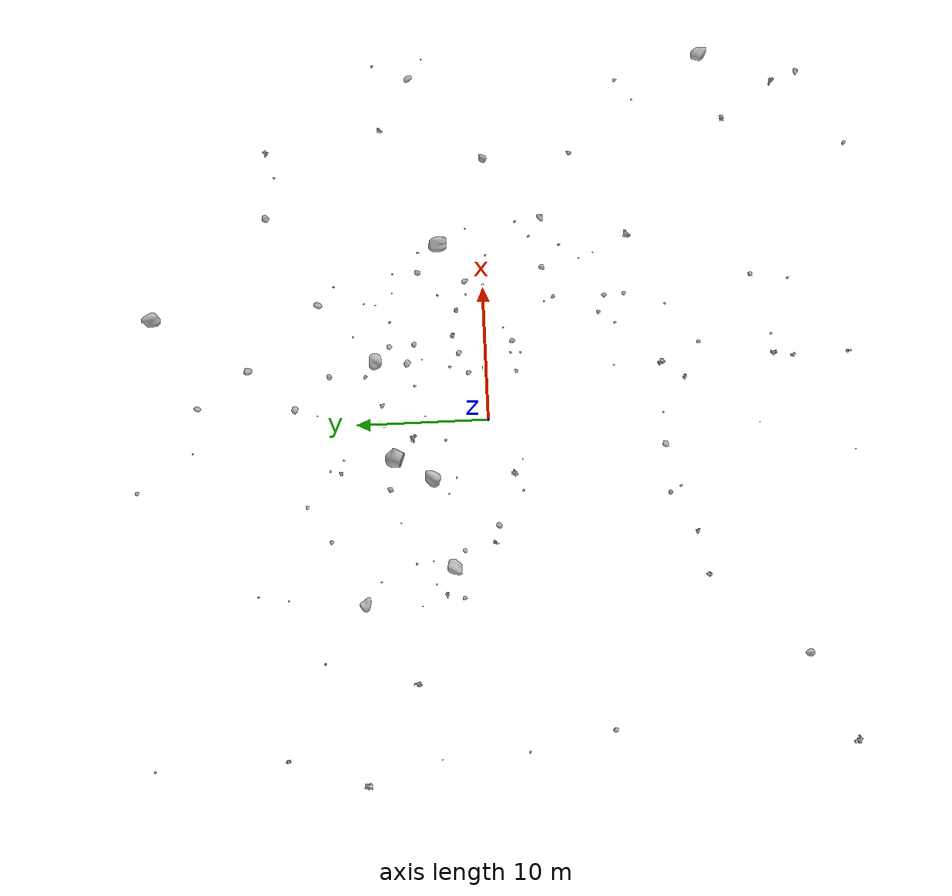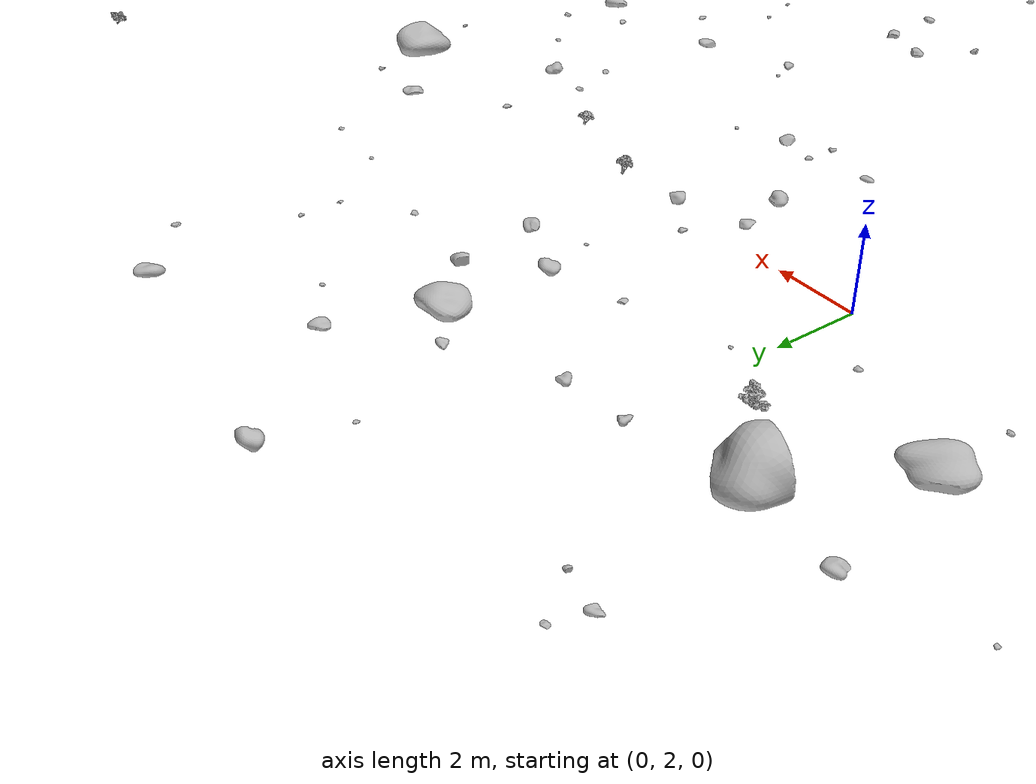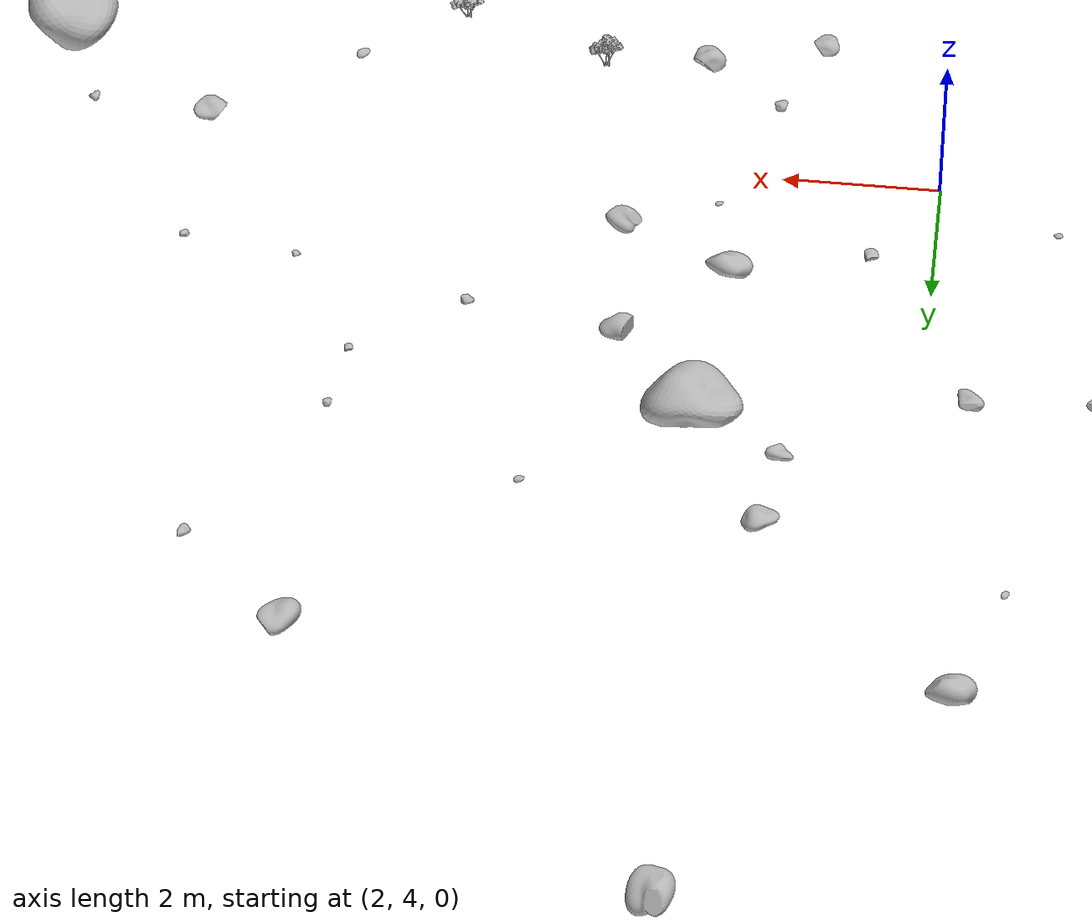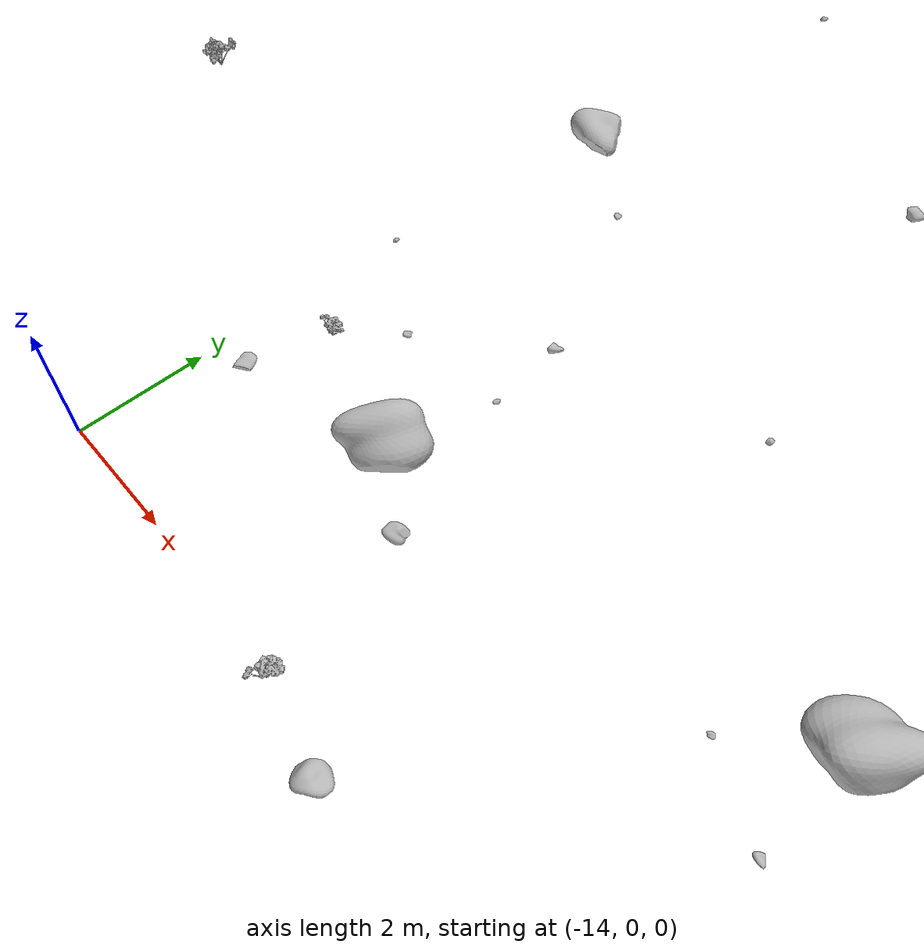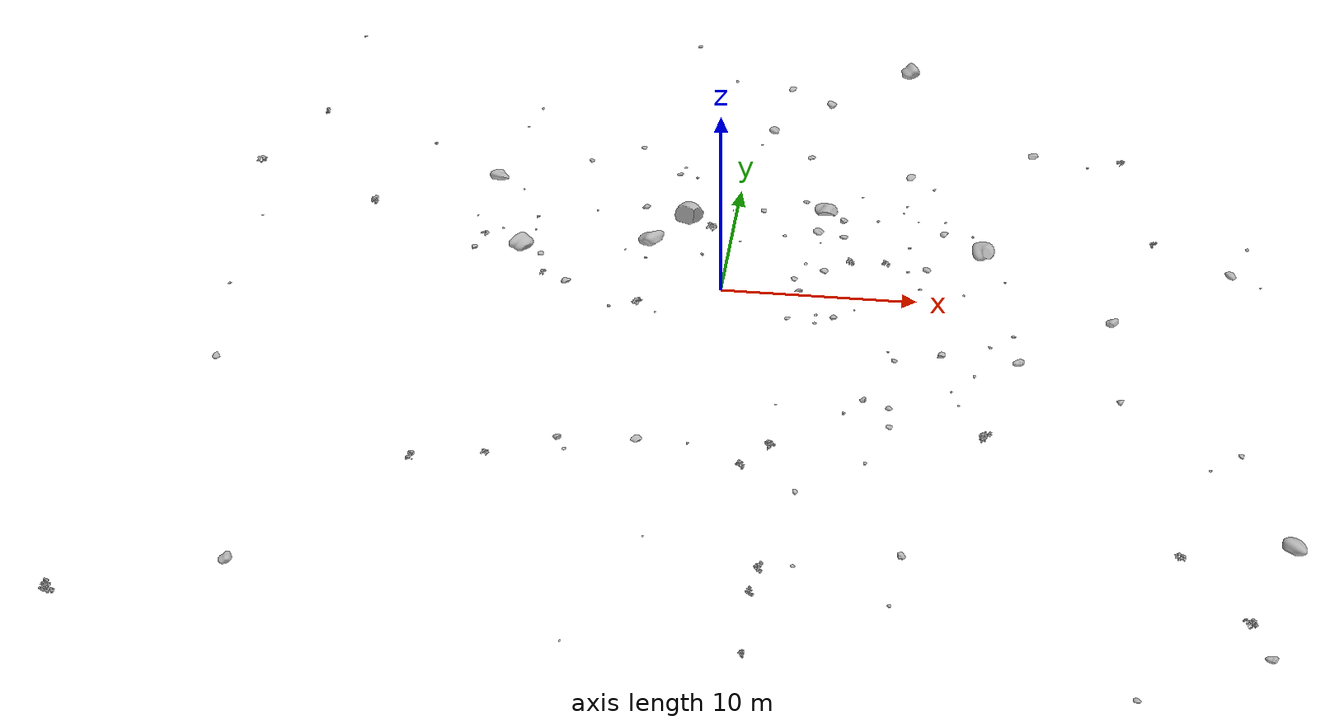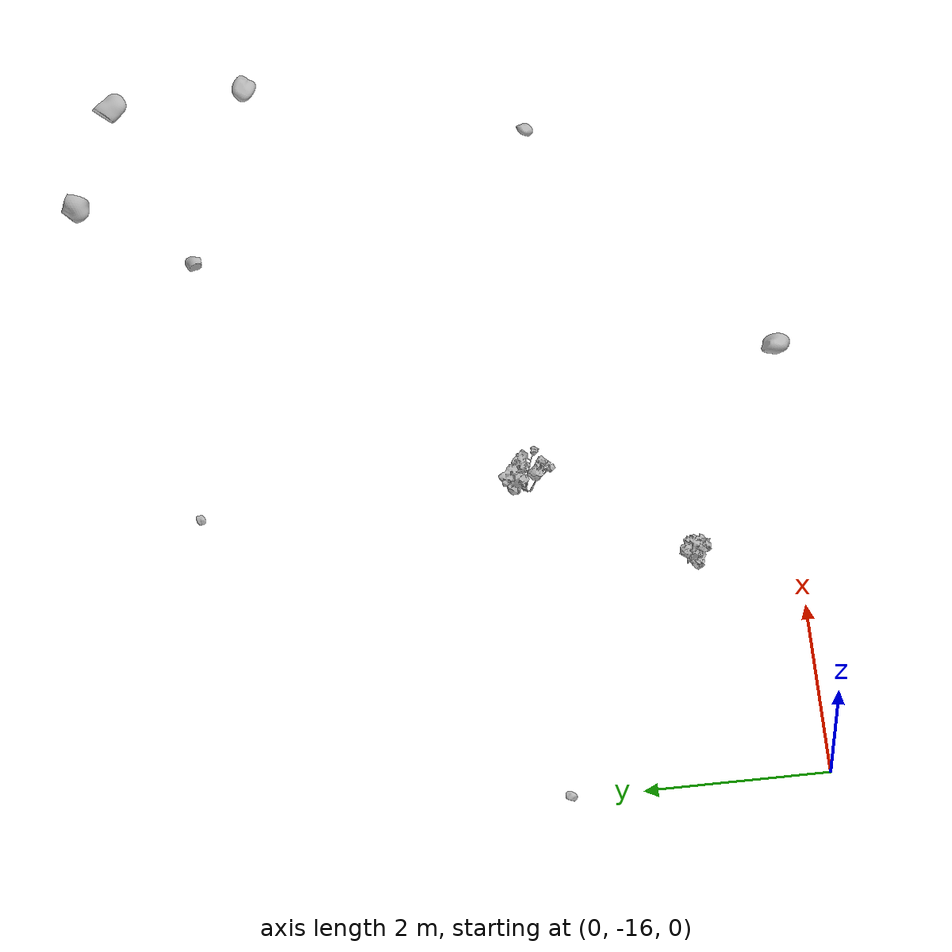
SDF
<sdf version="1.6">
 <world name="mars">
  <gravity>0 0 -9.81</gravity>
  <physics name="default_physics" type="ode">
   <max_step_size>0.001</max_step_size>
   <real_time_update_rate>1000</real_time_update_rate>
   <ode><solver><type>quick</type><iters>150</iters><sor>1.0</sor></solver></ode>
  </physics>
  <scene>
   <ambient>0.62 0.52 0.44 1</ambient>
   <background>0.83 0.66 0.50 1</background>
   <shadows>true</shadows>
   <grid>false</grid>
  </scene>
  <light name="sun" type="directional">
   <pose>0 0 30 0 0 0</pose>
   <diffuse>1 0.93 0.84 1</diffuse>
   <specular>0.1 0.1 0.1 1</specular>
   <direction>-0.45 0.35 -0.8</direction>
  </light>
  <model name="pebble_000">
   <static>true</static>
   <pose>-13.003 15.648 0.181 0 0 -3.029</pose>
   <link name="link">
    <collision name="collision">
     <geometry>
      <mesh><uri>model://mars_rocks/meshes/rock_2.dae</uri><scale>0.0770 0.0770 0.0716</scale></mesh>
     </geometry>
     <surface><friction><ode><mu>0.8</mu><mu2>0.8</mu2></ode></friction></surface>
    </collision>
    <visual name="visual">
     <geometry>
      <mesh><uri>model://mars_rocks/meshes/rock_2.dae</uri><scale>0.0770 0.0770 0.0716</scale></mesh>
     </geometry>
    </visual>
   </link>
  </model>
  <model name="pebble_001">
   <static>true</static>
   <pose>9.129 8.998 0.245 0 0 0.434</pose>
   <link name="link">
    <collision name="collision">
     <geometry>
      <mesh><uri>model://mars_rocks/meshes/rock_2.dae</uri><scale>0.0750 0.0750 0.0693</scale></mesh>
     </geometry>
     <surface><friction><ode><mu>0.8</mu><mu2>0.8</mu2></ode></friction></surface>
    </collision>
    <visual name="visual">
     <geometry>
      <mesh><uri>model://mars_rocks/meshes/rock_2.dae</uri><scale>0.0750 0.0750 0.0693</scale></mesh>
     </geometry>
    </visual>
   </link>
  </model>
  <model name="pebble_002">
   <static>true</static>
   <pose>12.334 -0.312 0.766 0 0 1.748</pose>
   <link name="link">
    <collision name="collision">
     <geometry>
      <mesh><uri>model://mars_rocks/meshes/rock_2.dae</uri><scale>0.0840 0.0840 0.0670</scale></mesh>
     </geometry>
     <surface><friction><ode><mu>0.8</mu><mu2>0.8</mu2></ode></friction></surface>
    </collision>
    <visual name="visual">
     <geometry>
      <mesh><uri>model://mars_rocks/meshes/rock_2.dae</uri><scale>0.0840 0.0840 0.0670</scale></mesh>
     </geometry>
    </visual>
   </link>
  </model>
  <model name="pebble_003">
   <static>true</static>
   <pose>0.476 4.754 0.037 0 0 -2.798</pose>
   <link name="link">
    <collision name="collision">
     <geometry>
      <mesh><uri>model://mars_rocks/meshes/rock_7.dae</uri><scale>0.0600 0.0600 0.0454</scale></mesh>
     </geometry>
     <surface><friction><ode><mu>0.8</mu><mu2>0.8</mu2></ode></friction></surface>
    </collision>
    <visual name="visual">
     <geometry>
      <mesh><uri>model://mars_rocks/meshes/rock_7.dae</uri><scale>0.0600 0.0600 0.0454</scale></mesh>
     </geometry>
    </visual>
   </link>
  </model>
  <model name="pebble_004">
   <static>true</static>
   <pose>-25.498 26.360 0.032 0 0 0.595</pose>
   <link name="link">
    <collision name="collision">
     <geometry>
      <mesh><uri>model://mars_rocks/meshes/rock_3.dae</uri><scale>0.1230 0.1230 0.0909</scale></mesh>
     </geometry>
     <surface><friction><ode><mu>0.8</mu><mu2>0.8</mu2></ode></friction></surface>
    </collision>
    <visual name="visual">
     <geometry>
      <mesh><uri>model://mars_rocks/meshes/rock_3.dae</uri><scale>0.1230 0.1230 0.0909</scale></mesh>
     </geometry>
    </visual>
   </link>
  </model>
  <model name="pebble_005">
   <static>true</static>
   <pose>-7.503 6.920 0.078 0 0 -1.441</pose>
   <link name="link">
    <collision name="collision">
     <geometry>
      <mesh><uri>model://mars_rocks/meshes/rock_4.dae</uri><scale>0.0740 0.0740 0.0710</scale></mesh>
     </geometry>
     <surface><friction><ode><mu>0.8</mu><mu2>0.8</mu2></ode></friction></surface>
    </collision>
    <visual name="visual">
     <geometry>
      <mesh><uri>model://mars_rocks/meshes/rock_4.dae</uri><scale>0.0740 0.0740 0.0710</scale></mesh>
     </geometry>
    </visual>
   </link>
  </model>
  <model name="pebble_006">
   <static>true</static>
   <pose>27.541 3.911 -0.360 0 0 -0.480</pose>
   <link name="link">
    <collision name="collision">
     <geometry>
      <mesh><uri>model://mars_rocks/meshes/rock_4.dae</uri><scale>0.0710 0.0710 0.0605</scale></mesh>
     </geometry>
     <surface><friction><ode><mu>0.8</mu><mu2>0.8</mu2></ode></friction></surface>
    </collision>
    <visual name="visual">
     <geometry>
      <mesh><uri>model://mars_rocks/meshes/rock_4.dae</uri><scale>0.0710 0.0710 0.0605</scale></mesh>
     </geometry>
    </visual>
   </link>
  </model>
  <model name="pebble_007">
   <static>true</static>
   <pose>11.228 6.718 0.757 0 0 0.779</pose>
   <link name="link">
    <collision name="collision">
     <geometry>
      <mesh><uri>model://mars_rocks/meshes/rock_0.dae</uri><scale>0.0780 0.0780 0.0747</scale></mesh>
     </geometry>
     <surface><friction><ode><mu>0.8</mu><mu2>0.8</mu2></ode></friction></surface>
    </collision>
    <visual name="visual">
     <geometry>
      <mesh><uri>model://mars_rocks/meshes/rock_0.dae</uri><scale>0.0780 0.0780 0.0747</scale></mesh>
     </geometry>
    </visual>
   </link>
  </model>
  <model name="pebble_008">
   <static>true</static>
   <pose>5.002 -1.871 0.061 0 0 -0.257</pose>
   <link name="link">
    <collision name="collision">
     <geometry>
      <mesh><uri>model://mars_rocks/meshes/rock_2.dae</uri><scale>0.1030 0.1030 0.0949</scale></mesh>
     </geometry>
     <surface><friction><ode><mu>0.8</mu><mu2>0.8</mu2></ode></friction></surface>
    </collision>
    <visual name="visual">
     <geometry>
      <mesh><uri>model://mars_rocks/meshes/rock_2.dae</uri><scale>0.1030 0.1030 0.0949</scale></mesh>
     </geometry>
    </visual>
   </link>
  </model>
  <model name="pebble_009">
   <static>true</static>
   <pose>-5.598 -14.280 0.070 0 0 -0.753</pose>
   <link name="link">
    <collision name="collision">
     <geometry>
      <mesh><uri>model://mars_rocks/meshes/rock_5.dae</uri><scale>0.1240 0.1240 0.0997</scale></mesh>
     </geometry>
     <surface><friction><ode><mu>0.8</mu><mu2>0.8</mu2></ode></friction></surface>
    </collision>
    <visual name="visual">
     <geometry>
      <mesh><uri>model://mars_rocks/meshes/rock_5.dae</uri><scale>0.1240 0.1240 0.0997</scale></mesh>
     </geometry>
    </visual>
   </link>
  </model>
  <model name="pebble_010">
   <static>true</static>
   <pose>12.675 4.707 1.164 0 0 -2.234</pose>
   <link name="link">
    <collision name="collision">
     <geometry>
      <mesh><uri>model://mars_rocks/meshes/rock_6.dae</uri><scale>0.0960 0.0960 0.0940</scale></mesh>
     </geometry>
     <surface><friction><ode><mu>0.8</mu><mu2>0.8</mu2></ode></friction></surface>
    </collision>
    <visual name="visual">
     <geometry>
      <mesh><uri>model://mars_rocks/meshes/rock_6.dae</uri><scale>0.0960 0.0960 0.0940</scale></mesh>
     </geometry>
    </visual>
   </link>
  </model>
  <model name="pebble_011">
   <static>true</static>
   <pose>27.182 7.651 -0.362 0 0 0.221</pose>
   <link name="link">
    <collision name="collision">
     <geometry>
      <mesh><uri>model://mars_rocks/meshes/rock_0.dae</uri><scale>0.1160 0.1160 0.1184</scale></mesh>
     </geometry>
     <surface><friction><ode><mu>0.8</mu><mu2>0.8</mu2></ode></friction></surface>
    </collision>
    <visual name="visual">
     <geometry>
      <mesh><uri>model://mars_rocks/meshes/rock_0.dae</uri><scale>0.1160 0.1160 0.1184</scale></mesh>
     </geometry>
    </visual>
   </link>
  </model>
  <model name="pebble_012">
   <static>true</static>
   <pose>6.908 -1.396 0.193 0 0 0.573</pose>
   <link name="link">
    <collision name="collision">
     <geometry>
      <mesh><uri>model://mars_rocks/meshes/rock_5.dae</uri><scale>0.0680 0.0680 0.0554</scale></mesh>
     </geometry>
     <surface><friction><ode><mu>0.8</mu><mu2>0.8</mu2></ode></friction></surface>
    </collision>
    <visual name="visual">
     <geometry>
      <mesh><uri>model://mars_rocks/meshes/rock_5.dae</uri><scale>0.0680 0.0680 0.0554</scale></mesh>
     </geometry>
    </visual>
   </link>
  </model>
  <model name="pebble_013">
   <static>true</static>
   <pose>-25.572 4.635 -0.113 0 0 2.769</pose>
   <link name="link">
    <collision name="collision">
     <geometry>
      <mesh><uri>model://mars_rocks/meshes/rock_4.dae</uri><scale>0.0810 0.0810 0.0668</scale></mesh>
     </geometry>
     <surface><friction><ode><mu>0.8</mu><mu2>0.8</mu2></ode></friction></surface>
    </collision>
    <visual name="visual">
     <geometry>
      <mesh><uri>model://mars_rocks/meshes/rock_4.dae</uri><scale>0.0810 0.0810 0.0668</scale></mesh>
     </geometry>
    </visual>
   </link>
  </model>
  <model name="pebble_014">
   <static>true</static>
   <pose>8.762 -4.598 -0.019 0 0 0.768</pose>
   <link name="link">
    <collision name="collision">
     <geometry>
      <mesh><uri>model://mars_rocks/meshes/rock_2.dae</uri><scale>0.0620 0.0620 0.0626</scale></mesh>
     </geometry>
     <surface><friction><ode><mu>0.8</mu><mu2>0.8</mu2></ode></friction></surface>
    </collision>
    <visual name="visual">
     <geometry>
      <mesh><uri>model://mars_rocks/meshes/rock_2.dae</uri><scale>0.0620 0.0620 0.0626</scale></mesh>
     </geometry>
    </visual>
   </link>
  </model>
  <model name="pebble_015">
   <static>true</static>
   <pose>14.878 -2.614 0.017 0 0 -0.717</pose>
   <link name="link">
    <collision name="collision">
     <geometry>
      <mesh><uri>model://mars_rocks/meshes/rock_6.dae</uri><scale>0.1220 0.1220 0.0920</scale></mesh>
     </geometry>
     <surface><friction><ode><mu>0.8</mu><mu2>0.8</mu2></ode></friction></surface>
    </collision>
    <visual name="visual">
     <geometry>
      <mesh><uri>model://mars_rocks/meshes/rock_6.dae</uri><scale>0.1220 0.1220 0.0920</scale></mesh>
     </geometry>
    </visual>
   </link>
  </model>
  <model name="pebble_016">
   <static>true</static>
   <pose>-0.011 -13.220 0.093 0 0 3.022</pose>
   <link name="link">
    <collision name="collision">
     <geometry>
      <mesh><uri>model://mars_rocks/meshes/rock_2.dae</uri><scale>0.0710 0.0710 0.0650</scale></mesh>
     </geometry>
     <surface><friction><ode><mu>0.8</mu><mu2>0.8</mu2></ode></friction></surface>
    </collision>
    <visual name="visual">
     <geometry>
      <mesh><uri>model://mars_rocks/meshes/rock_2.dae</uri><scale>0.0710 0.0710 0.0650</scale></mesh>
     </geometry>
    </visual>
   </link>
  </model>
  <model name="pebble_017">
   <static>true</static>
   <pose>-2.596 11.015 0.093 0 0 2.907</pose>
   <link name="link">
    <collision name="collision">
     <geometry>
      <mesh><uri>model://mars_rocks/meshes/rock_1.dae</uri><scale>0.0980 0.0980 0.0795</scale></mesh>
     </geometry>
     <surface><friction><ode><mu>0.8</mu><mu2>0.8</mu2></ode></friction></surface>
    </collision>
    <visual name="visual">
     <geometry>
      <mesh><uri>model://mars_rocks/meshes/rock_1.dae</uri><scale>0.0980 0.0980 0.0795</scale></mesh>
     </geometry>
    </visual>
   </link>
  </model>
  <model name="pebble_018">
   <static>true</static>
   <pose>23.816 -11.885 -0.385 0 0 -0.177</pose>
   <link name="link">
    <collision name="collision">
     <geometry>
      <mesh><uri>model://mars_rocks/meshes/rock_4.dae</uri><scale>0.0830 0.0830 0.0881</scale></mesh>
     </geometry>
     <surface><friction><ode><mu>0.8</mu><mu2>0.8</mu2></ode></friction></surface>
    </collision>
    <visual name="visual">
     <geometry>
      <mesh><uri>model://mars_rocks/meshes/rock_4.dae</uri><scale>0.0830 0.0830 0.0881</scale></mesh>
     </geometry>
    </visual>
   </link>
  </model>
  <model name="pebble_019">
   <static>true</static>
   <pose>-17.870 13.111 0.156 0 0 -0.587</pose>
   <link name="link">
    <collision name="collision">
     <geometry>
      <mesh><uri>model://mars_rocks/meshes/rock_1.dae</uri><scale>0.1100 0.1100 0.1132</scale></mesh>
     </geometry>
     <surface><friction><ode><mu>0.8</mu><mu2>0.8</mu2></ode></friction></surface>
    </collision>
    <visual name="visual">
     <geometry>
      <mesh><uri>model://mars_rocks/meshes/rock_1.dae</uri><scale>0.1100 0.1100 0.1132</scale></mesh>
     </geometry>
    </visual>
   </link>
  </model>
  <model name="pebble_020">
   <static>true</static>
   <pose>5.001 -2.616 0.046 0 0 -1.123</pose>
   <link name="link">
    <collision name="collision">
     <geometry>
      <mesh><uri>model://mars_rocks/meshes/rock_5.dae</uri><scale>0.1060 0.1060 0.1146</scale></mesh>
     </geometry>
     <surface><friction><ode><mu>0.8</mu><mu2>0.8</mu2></ode></friction></surface>
    </collision>
    <visual name="visual">
     <geometry>
      <mesh><uri>model://mars_rocks/meshes/rock_5.dae</uri><scale>0.1060 0.1060 0.1146</scale></mesh>
     </geometry>
    </visual>
   </link>
  </model>
  <model name="pebble_021">
   <static>true</static>
   <pose>-12.242 4.471 0.112 0 0 0.880</pose>
   <link name="link">
    <collision name="collision">
     <geometry>
      <mesh><uri>model://mars_rocks/meshes/rock_4.dae</uri><scale>0.0820 0.0820 0.0731</scale></mesh>
     </geometry>
     <surface><friction><ode><mu>0.8</mu><mu2>0.8</mu2></ode></friction></surface>
    </collision>
    <visual name="visual">
     <geometry>
      <mesh><uri>model://mars_rocks/meshes/rock_4.dae</uri><scale>0.0820 0.0820 0.0731</scale></mesh>
     </geometry>
    </visual>
   </link>
  </model>
  <model name="pebble_022">
   <static>true</static>
   <pose>9.732 -23.080 -0.155 0 0 2.294</pose>
   <link name="link">
    <collision name="collision">
     <geometry>
      <mesh><uri>model://mars_rocks/meshes/rock_7.dae</uri><scale>0.1150 0.1150 0.1117</scale></mesh>
     </geometry>
     <surface><friction><ode><mu>0.8</mu><mu2>0.8</mu2></ode></friction></surface>
    </collision>
    <visual name="visual">
     <geometry>
      <mesh><uri>model://mars_rocks/meshes/rock_7.dae</uri><scale>0.1150 0.1150 0.1117</scale></mesh>
     </geometry>
    </visual>
   </link>
  </model>
  <model name="pebble_023">
   <static>true</static>
   <pose>12.309 -8.438 -0.202 0 0 -0.101</pose>
   <link name="link">
    <collision name="collision">
     <geometry>
      <mesh><uri>model://mars_rocks/meshes/rock_5.dae</uri><scale>0.0690 0.0690 0.0655</scale></mesh>
     </geometry>
     <surface><friction><ode><mu>0.8</mu><mu2>0.8</mu2></ode></friction></surface>
    </collision>
    <visual name="visual">
     <geometry>
      <mesh><uri>model://mars_rocks/meshes/rock_5.dae</uri><scale>0.0690 0.0690 0.0655</scale></mesh>
     </geometry>
    </visual>
   </link>
  </model>
  <model name="pebble_024">
   <static>true</static>
   <pose>10.525 11.237 0.086 0 0 0.638</pose>
   <link name="link">
    <collision name="collision">
     <geometry>
      <mesh><uri>model://mars_rocks/meshes/rock_6.dae</uri><scale>0.1120 0.1120 0.1046</scale></mesh>
     </geometry>
     <surface><friction><ode><mu>0.8</mu><mu2>0.8</mu2></ode></friction></surface>
    </collision>
    <visual name="visual">
     <geometry>
      <mesh><uri>model://mars_rocks/meshes/rock_6.dae</uri><scale>0.1120 0.1120 0.1046</scale></mesh>
     </geometry>
    </visual>
   </link>
  </model>
  <model name="pebble_025">
   <static>true</static>
   <pose>0.845 12.660 1.521 0 0 0.996</pose>
   <link name="link">
    <collision name="collision">
     <geometry>
      <mesh><uri>model://mars_rocks/meshes/rock_3.dae</uri><scale>0.0700 0.0700 0.0680</scale></mesh>
     </geometry>
     <surface><friction><ode><mu>0.8</mu><mu2>0.8</mu2></ode></friction></surface>
    </collision>
    <visual name="visual">
     <geometry>
      <mesh><uri>model://mars_rocks/meshes/rock_3.dae</uri><scale>0.0700 0.0700 0.0680</scale></mesh>
     </geometry>
    </visual>
   </link>
  </model>
  <model name="pebble_026">
   <static>true</static>
   <pose>9.826 6.808 0.645 0 0 -1.113</pose>
   <link name="link">
    <collision name="collision">
     <geometry>
      <mesh><uri>model://mars_rocks/meshes/rock_0.dae</uri><scale>0.0620 0.0620 0.0551</scale></mesh>
     </geometry>
     <surface><friction><ode><mu>0.8</mu><mu2>0.8</mu2></ode></friction></surface>
    </collision>
    <visual name="visual">
     <geometry>
      <mesh><uri>model://mars_rocks/meshes/rock_0.dae</uri><scale>0.0620 0.0620 0.0551</scale></mesh>
     </geometry>
    </visual>
   </link>
  </model>
  <model name="pebble_027">
   <static>true</static>
   <pose>13.009 -5.912 -0.232 0 0 1.398</pose>
   <link name="link">
    <collision name="collision">
     <geometry>
      <mesh><uri>model://mars_rocks/meshes/rock_3.dae</uri><scale>0.1220 0.1220 0.1226</scale></mesh>
     </geometry>
     <surface><friction><ode><mu>0.8</mu><mu2>0.8</mu2></ode></friction></surface>
    </collision>
    <visual name="visual">
     <geometry>
      <mesh><uri>model://mars_rocks/meshes/rock_3.dae</uri><scale>0.1220 0.1220 0.1226</scale></mesh>
     </geometry>
    </visual>
   </link>
  </model>
  <model name="pebble_028">
   <static>true</static>
   <pose>5.544 -21.524 0.283 0 0 -1.358</pose>
   <link name="link">
    <collision name="collision">
     <geometry>
      <mesh><uri>model://mars_rocks/meshes/rock_5.dae</uri><scale>0.1130 0.1130 0.1210</scale></mesh>
     </geometry>
     <surface><friction><ode><mu>0.8</mu><mu2>0.8</mu2></ode></friction></surface>
    </collision>
    <visual name="visual">
     <geometry>
      <mesh><uri>model://mars_rocks/meshes/rock_5.dae</uri><scale>0.1130 0.1130 0.1210</scale></mesh>
     </geometry>
    </visual>
   </link>
  </model>
  <model name="pebble_029">
   <static>true</static>
   <pose>9.432 3.388 1.088 0 0 0.727</pose>
   <link name="link">
    <collision name="collision">
     <geometry>
      <mesh><uri>model://mars_rocks/meshes/rock_3.dae</uri><scale>0.1120 0.1120 0.0989</scale></mesh>
     </geometry>
     <surface><friction><ode><mu>0.8</mu><mu2>0.8</mu2></ode></friction></surface>
    </collision>
    <visual name="visual">
     <geometry>
      <mesh><uri>model://mars_rocks/meshes/rock_3.dae</uri><scale>0.1120 0.1120 0.0989</scale></mesh>
     </geometry>
    </visual>
   </link>
  </model>
  <model name="pebble_030">
   <static>true</static>
   <pose>8.188 -13.666 -0.006 0 0 0.674</pose>
   <link name="link">
    <collision name="collision">
     <geometry>
      <mesh><uri>model://mars_rocks/meshes/rock_4.dae</uri><scale>0.1100 0.1100 0.1171</scale></mesh>
     </geometry>
     <surface><friction><ode><mu>0.8</mu><mu2>0.8</mu2></ode></friction></surface>
    </collision>
    <visual name="visual">
     <geometry>
      <mesh><uri>model://mars_rocks/meshes/rock_4.dae</uri><scale>0.1100 0.1100 0.1171</scale></mesh>
     </geometry>
    </visual>
   </link>
  </model>
  <model name="pebble_031">
   <static>true</static>
   <pose>-3.393 -27.457 0.526 0 0 -1.678</pose>
   <link name="link">
    <collision name="collision">
     <geometry>
      <mesh><uri>model://mars_rocks/meshes/rock_3.dae</uri><scale>0.0620 0.0620 0.0513</scale></mesh>
     </geometry>
     <surface><friction><ode><mu>0.8</mu><mu2>0.8</mu2></ode></friction></surface>
    </collision>
    <visual name="visual">
     <geometry>
      <mesh><uri>model://mars_rocks/meshes/rock_3.dae</uri><scale>0.0620 0.0620 0.0513</scale></mesh>
     </geometry>
    </visual>
   </link>
  </model>
  <model name="pebble_032">
   <static>true</static>
   <pose>-1.381 3.294 -0.014 0 0 -2.101</pose>
   <link name="link">
    <collision name="collision">
     <geometry>
      <mesh><uri>model://mars_rocks/meshes/rock_5.dae</uri><scale>0.1080 0.1080 0.1098</scale></mesh>
     </geometry>
     <surface><friction><ode><mu>0.8</mu><mu2>0.8</mu2></ode></friction></surface>
    </collision>
    <visual name="visual">
     <geometry>
      <mesh><uri>model://mars_rocks/meshes/rock_5.dae</uri><scale>0.1080 0.1080 0.1098</scale></mesh>
     </geometry>
    </visual>
   </link>
  </model>
  <model name="pebble_033">
   <static>true</static>
   <pose>-10.481 4.614 0.076 0 0 -2.438</pose>
   <link name="link">
    <collision name="collision">
     <geometry>
      <mesh><uri>model://mars_rocks/meshes/rock_6.dae</uri><scale>0.0660 0.0660 0.0623</scale></mesh>
     </geometry>
     <surface><friction><ode><mu>0.8</mu><mu2>0.8</mu2></ode></friction></surface>
    </collision>
    <visual name="visual">
     <geometry>
      <mesh><uri>model://mars_rocks/meshes/rock_6.dae</uri><scale>0.0660 0.0660 0.0623</scale></mesh>
     </geometry>
    </visual>
   </link>
  </model>
  <model name="pebble_034">
   <static>true</static>
   <pose>-12.595 17.927 0.181 0 0 0.405</pose>
   <link name="link">
    <collision name="collision">
     <geometry>
      <mesh><uri>model://mars_rocks/meshes/rock_0.dae</uri><scale>0.0980 0.0980 0.0953</scale></mesh>
     </geometry>
     <surface><friction><ode><mu>0.8</mu><mu2>0.8</mu2></ode></friction></surface>
    </collision>
    <visual name="visual">
     <geometry>
      <mesh><uri>model://mars_rocks/meshes/rock_0.dae</uri><scale>0.0980 0.0980 0.0953</scale></mesh>
     </geometry>
    </visual>
   </link>
  </model>
  <model name="pebble_035">
   <static>true</static>
   <pose>6.941 -9.884 -0.078 0 0 -2.810</pose>
   <link name="link">
    <collision name="collision">
     <geometry>
      <mesh><uri>model://mars_rocks/meshes/rock_1.dae</uri><scale>0.1140 0.1140 0.1175</scale></mesh>
     </geometry>
     <surface><friction><ode><mu>0.8</mu><mu2>0.8</mu2></ode></friction></surface>
    </collision>
    <visual name="visual">
     <geometry>
      <mesh><uri>model://mars_rocks/meshes/rock_1.dae</uri><scale>0.1140 0.1140 0.1175</scale></mesh>
     </geometry>
    </visual>
   </link>
  </model>
  <model name="pebble_036">
   <static>true</static>
   <pose>-5.449 3.220 0.056 0 0 0.476</pose>
   <link name="link">
    <collision name="collision">
     <geometry>
      <mesh><uri>model://mars_rocks/meshes/rock_7.dae</uri><scale>0.0610 0.0610 0.0479</scale></mesh>
     </geometry>
     <surface><friction><ode><mu>0.8</mu><mu2>0.8</mu2></ode></friction></surface>
    </collision>
    <visual name="visual">
     <geometry>
      <mesh><uri>model://mars_rocks/meshes/rock_7.dae</uri><scale>0.0610 0.0610 0.0479</scale></mesh>
     </geometry>
    </visual>
   </link>
  </model>
  <model name="pebble_037">
   <static>true</static>
   <pose>9.451 1.295 0.937 0 0 2.131</pose>
   <link name="link">
    <collision name="collision">
     <geometry>
      <mesh><uri>model://mars_rocks/meshes/rock_5.dae</uri><scale>0.1010 0.1010 0.0938</scale></mesh>
     </geometry>
     <surface><friction><ode><mu>0.8</mu><mu2>0.8</mu2></ode></friction></surface>
    </collision>
    <visual name="visual">
     <geometry>
      <mesh><uri>model://mars_rocks/meshes/rock_5.dae</uri><scale>0.1010 0.1010 0.0938</scale></mesh>
     </geometry>
    </visual>
   </link>
  </model>
  <model name="pebble_038">
   <static>true</static>
   <pose>6.682 9.937 0.105 0 0 0.190</pose>
   <link name="link">
    <collision name="collision">
     <geometry>
      <mesh><uri>model://mars_rocks/meshes/rock_3.dae</uri><scale>0.0780 0.0780 0.0814</scale></mesh>
     </geometry>
     <surface><friction><ode><mu>0.8</mu><mu2>0.8</mu2></ode></friction></surface>
    </collision>
    <visual name="visual">
     <geometry>
      <mesh><uri>model://mars_rocks/meshes/rock_3.dae</uri><scale>0.0780 0.0780 0.0814</scale></mesh>
     </geometry>
    </visual>
   </link>
  </model>
  <model name="pebble_039">
   <static>true</static>
   <pose>-3.087 -2.445 -0.000 0 0 1.946</pose>
   <link name="link">
    <collision name="collision">
     <geometry>
      <mesh><uri>model://mars_rocks/meshes/rock_1.dae</uri><scale>0.0630 0.0630 0.0468</scale></mesh>
     </geometry>
     <surface><friction><ode><mu>0.8</mu><mu2>0.8</mu2></ode></friction></surface>
    </collision>
    <visual name="visual">
     <geometry>
      <mesh><uri>model://mars_rocks/meshes/rock_1.dae</uri><scale>0.0630 0.0630 0.0468</scale></mesh>
     </geometry>
    </visual>
   </link>
  </model>
  <model name="pebble_040">
   <static>true</static>
   <pose>3.722 -9.647 0.013 0 0 -2.765</pose>
   <link name="link">
    <collision name="collision">
     <geometry>
      <mesh><uri>model://mars_rocks/meshes/rock_4.dae</uri><scale>0.0700 0.0700 0.0563</scale></mesh>
     </geometry>
     <surface><friction><ode><mu>0.8</mu><mu2>0.8</mu2></ode></friction></surface>
    </collision>
    <visual name="visual">
     <geometry>
      <mesh><uri>model://mars_rocks/meshes/rock_4.dae</uri><scale>0.0700 0.0700 0.0563</scale></mesh>
     </geometry>
    </visual>
   </link>
  </model>
  <model name="pebble_041">
   <static>true</static>
   <pose>2.790 5.455 0.102 0 0 -0.203</pose>
   <link name="link">
    <collision name="collision">
     <geometry>
      <mesh><uri>model://mars_rocks/meshes/rock_5.dae</uri><scale>0.1200 0.1200 0.0889</scale></mesh>
     </geometry>
     <surface><friction><ode><mu>0.8</mu><mu2>0.8</mu2></ode></friction></surface>
    </collision>
    <visual name="visual">
     <geometry>
      <mesh><uri>model://mars_rocks/meshes/rock_5.dae</uri><scale>0.1200 0.1200 0.0889</scale></mesh>
     </geometry>
    </visual>
   </link>
  </model>
  <model name="pebble_042">
   <static>true</static>
   <pose>-11.900 8.609 0.144 0 0 2.034</pose>
   <link name="link">
    <collision name="collision">
     <geometry>
      <mesh><uri>model://mars_rocks/meshes/rock_4.dae</uri><scale>0.0870 0.0870 0.0689</scale></mesh>
     </geometry>
     <surface><friction><ode><mu>0.8</mu><mu2>0.8</mu2></ode></friction></surface>
    </collision>
    <visual name="visual">
     <geometry>
      <mesh><uri>model://mars_rocks/meshes/rock_4.dae</uri><scale>0.0870 0.0870 0.0689</scale></mesh>
     </geometry>
    </visual>
   </link>
  </model>
  <model name="pebble_043">
   <static>true</static>
   <pose>4.737 4.810 0.222 0 0 0.285</pose>
   <link name="link">
    <collision name="collision">
     <geometry>
      <mesh><uri>model://mars_rocks/meshes/rock_3.dae</uri><scale>0.0610 0.0610 0.0542</scale></mesh>
     </geometry>
     <surface><friction><ode><mu>0.8</mu><mu2>0.8</mu2></ode></friction></surface>
    </collision>
    <visual name="visual">
     <geometry>
      <mesh><uri>model://mars_rocks/meshes/rock_3.dae</uri><scale>0.0610 0.0610 0.0542</scale></mesh>
     </geometry>
    </visual>
   </link>
  </model>
  <model name="pebble_044">
   <static>true</static>
   <pose>-13.826 5.560 0.160 0 0 -1.497</pose>
   <link name="link">
    <collision name="collision">
     <geometry>
      <mesh><uri>model://mars_rocks/meshes/rock_4.dae</uri><scale>0.0620 0.0620 0.0651</scale></mesh>
     </geometry>
     <surface><friction><ode><mu>0.8</mu><mu2>0.8</mu2></ode></friction></surface>
    </collision>
    <visual name="visual">
     <geometry>
      <mesh><uri>model://mars_rocks/meshes/rock_4.dae</uri><scale>0.0620 0.0620 0.0651</scale></mesh>
     </geometry>
    </visual>
   </link>
  </model>
  <model name="pebble_045">
   <static>true</static>
   <pose>-3.363 12.060 0.126 0 0 2.253</pose>
   <link name="link">
    <collision name="collision">
     <geometry>
      <mesh><uri>model://mars_rocks/meshes/rock_2.dae</uri><scale>0.0970 0.0970 0.0714</scale></mesh>
     </geometry>
     <surface><friction><ode><mu>0.8</mu><mu2>0.8</mu2></ode></friction></surface>
    </collision>
    <visual name="visual">
     <geometry>
      <mesh><uri>model://mars_rocks/meshes/rock_2.dae</uri><scale>0.0970 0.0970 0.0714</scale></mesh>
     </geometry>
    </visual>
   </link>
  </model>
  <model name="pebble_046">
   <static>true</static>
   <pose>13.727 -3.623 -0.051 0 0 1.759</pose>
   <link name="link">
    <collision name="collision">
     <geometry>
      <mesh><uri>model://mars_rocks/meshes/rock_6.dae</uri><scale>0.1280 0.1280 0.1023</scale></mesh>
     </geometry>
     <surface><friction><ode><mu>0.8</mu><mu2>0.8</mu2></ode></friction></surface>
    </collision>
    <visual name="visual">
     <geometry>
      <mesh><uri>model://mars_rocks/meshes/rock_6.dae</uri><scale>0.1280 0.1280 0.1023</scale></mesh>
     </geometry>
    </visual>
   </link>
  </model>
  <model name="pebble_047">
   <static>true</static>
   <pose>-1.052 -20.378 0.362 0 0 -1.296</pose>
   <link name="link">
    <collision name="collision">
     <geometry>
      <mesh><uri>model://mars_rocks/meshes/rock_3.dae</uri><scale>0.0600 0.0600 0.0592</scale></mesh>
     </geometry>
     <surface><friction><ode><mu>0.8</mu><mu2>0.8</mu2></ode></friction></surface>
    </collision>
    <visual name="visual">
     <geometry>
      <mesh><uri>model://mars_rocks/meshes/rock_3.dae</uri><scale>0.0600 0.0600 0.0592</scale></mesh>
     </geometry>
    </visual>
   </link>
  </model>
  <model name="pebble_048">
   <static>true</static>
   <pose>7.668 7.109 0.356 0 0 -1.076</pose>
   <link name="link">
    <collision name="collision">
     <geometry>
      <mesh><uri>model://mars_rocks/meshes/rock_0.dae</uri><scale>0.0980 0.0980 0.0886</scale></mesh>
     </geometry>
     <surface><friction><ode><mu>0.8</mu><mu2>0.8</mu2></ode></friction></surface>
    </collision>
    <visual name="visual">
     <geometry>
      <mesh><uri>model://mars_rocks/meshes/rock_0.dae</uri><scale>0.0980 0.0980 0.0886</scale></mesh>
     </geometry>
    </visual>
   </link>
  </model>
  <model name="pebble_049">
   <static>true</static>
   <pose>11.943 -7.374 -0.200 0 0 -2.090</pose>
   <link name="link">
    <collision name="collision">
     <geometry>
      <mesh><uri>model://mars_rocks/meshes/rock_6.dae</uri><scale>0.0770 0.0770 0.0802</scale></mesh>
     </geometry>
     <surface><friction><ode><mu>0.8</mu><mu2>0.8</mu2></ode></friction></surface>
    </collision>
    <visual name="visual">
     <geometry>
      <mesh><uri>model://mars_rocks/meshes/rock_6.dae</uri><scale>0.0770 0.0770 0.0802</scale></mesh>
     </geometry>
    </visual>
   </link>
  </model>
  <model name="pebble_050">
   <static>true</static>
   <pose>14.373 1.121 0.784 0 0 0.989</pose>
   <link name="link">
    <collision name="collision">
     <geometry>
      <mesh><uri>model://mars_rocks/meshes/rock_6.dae</uri><scale>0.0760 0.0760 0.0681</scale></mesh>
     </geometry>
     <surface><friction><ode><mu>0.8</mu><mu2>0.8</mu2></ode></friction></surface>
    </collision>
    <visual name="visual">
     <geometry>
      <mesh><uri>model://mars_rocks/meshes/rock_6.dae</uri><scale>0.0760 0.0760 0.0681</scale></mesh>
     </geometry>
    </visual>
   </link>
  </model>
  <model name="pebble_051">
   <static>true</static>
   <pose>-1.606 22.347 0.322 0 0 1.446</pose>
   <link name="link">
    <collision name="collision">
     <geometry>
      <mesh><uri>model://mars_rocks/meshes/rock_1.dae</uri><scale>0.1000 0.1000 0.1058</scale></mesh>
     </geometry>
     <surface><friction><ode><mu>0.8</mu><mu2>0.8</mu2></ode></friction></surface>
    </collision>
    <visual name="visual">
     <geometry>
      <mesh><uri>model://mars_rocks/meshes/rock_1.dae</uri><scale>0.1000 0.1000 0.1058</scale></mesh>
     </geometry>
    </visual>
   </link>
  </model>
  <model name="pebble_052">
   <static>true</static>
   <pose>10.107 -0.042 0.777 0 0 2.870</pose>
   <link name="link">
    <collision name="collision">
     <geometry>
      <mesh><uri>model://mars_rocks/meshes/rock_4.dae</uri><scale>0.1050 0.1050 0.0751</scale></mesh>
     </geometry>
     <surface><friction><ode><mu>0.8</mu><mu2>0.8</mu2></ode></friction></surface>
    </collision>
    <visual name="visual">
     <geometry>
      <mesh><uri>model://mars_rocks/meshes/rock_4.dae</uri><scale>0.1050 0.1050 0.0751</scale></mesh>
     </geometry>
    </visual>
   </link>
  </model>
  <model name="pebble_053">
   <static>true</static>
   <pose>-25.302 -2.019 -0.220 0 0 2.280</pose>
   <link name="link">
    <collision name="collision">
     <geometry>
      <mesh><uri>model://mars_rocks/meshes/rock_2.dae</uri><scale>0.1090 0.1090 0.0893</scale></mesh>
     </geometry>
     <surface><friction><ode><mu>0.8</mu><mu2>0.8</mu2></ode></friction></surface>
    </collision>
    <visual name="visual">
     <geometry>
      <mesh><uri>model://mars_rocks/meshes/rock_2.dae</uri><scale>0.1090 0.1090 0.0893</scale></mesh>
     </geometry>
    </visual>
   </link>
  </model>
  <model name="pebble_054">
   <static>true</static>
   <pose>19.038 15.424 -0.317 0 0 -0.222</pose>
   <link name="link">
    <collision name="collision">
     <geometry>
      <mesh><uri>model://mars_rocks/meshes/rock_2.dae</uri><scale>0.0920 0.0920 0.0984</scale></mesh>
     </geometry>
     <surface><friction><ode><mu>0.8</mu><mu2>0.8</mu2></ode></friction></surface>
    </collision>
    <visual name="visual">
     <geometry>
      <mesh><uri>model://mars_rocks/meshes/rock_2.dae</uri><scale>0.0920 0.0920 0.0984</scale></mesh>
     </geometry>
    </visual>
   </link>
  </model>
  <model name="pebble_055">
   <static>true</static>
   <pose>-10.611 5.896 0.089 0 0 0.194</pose>
   <link name="link">
    <collision name="collision">
     <geometry>
      <mesh><uri>model://mars_rocks/meshes/rock_6.dae</uri><scale>0.1270 0.1270 0.1346</scale></mesh>
     </geometry>
     <surface><friction><ode><mu>0.8</mu><mu2>0.8</mu2></ode></friction></surface>
    </collision>
    <visual name="visual">
     <geometry>
      <mesh><uri>model://mars_rocks/meshes/rock_6.dae</uri><scale>0.1270 0.1270 0.1346</scale></mesh>
     </geometry>
    </visual>
   </link>
  </model>
  <model name="pebble_056">
   <static>true</static>
   <pose>-5.427 -2.399 0.147 0 0 2.772</pose>
   <link name="link">
    <collision name="collision">
     <geometry>
      <mesh><uri>model://mars_rocks/meshes/rock_7.dae</uri><scale>0.1150 0.1150 0.0875</scale></mesh>
     </geometry>
     <surface><friction><ode><mu>0.8</mu><mu2>0.8</mu2></ode></friction></surface>
    </collision>
    <visual name="visual">
     <geometry>
      <mesh><uri>model://mars_rocks/meshes/rock_7.dae</uri><scale>0.1150 0.1150 0.0875</scale></mesh>
     </geometry>
    </visual>
   </link>
  </model>
  <model name="pebble_057">
   <static>true</static>
   <pose>4.118 2.724 0.146 0 0 0.317</pose>
   <link name="link">
    <collision name="collision">
     <geometry>
      <mesh><uri>model://mars_rocks/meshes/rock_2.dae</uri><scale>0.1100 0.1100 0.0978</scale></mesh>
     </geometry>
     <surface><friction><ode><mu>0.8</mu><mu2>0.8</mu2></ode></friction></surface>
    </collision>
    <visual name="visual">
     <geometry>
      <mesh><uri>model://mars_rocks/meshes/rock_2.dae</uri><scale>0.1100 0.1100 0.0978</scale></mesh>
     </geometry>
    </visual>
   </link>
  </model>
  <model name="pebble_058">
   <static>true</static>
   <pose>-4.253 2.596 0.012 0 0 -0.930</pose>
   <link name="link">
    <collision name="collision">
     <geometry>
      <mesh><uri>model://mars_rocks/meshes/rock_6.dae</uri><scale>0.1010 0.1010 0.0945</scale></mesh>
     </geometry>
     <surface><friction><ode><mu>0.8</mu><mu2>0.8</mu2></ode></friction></surface>
    </collision>
    <visual name="visual">
     <geometry>
      <mesh><uri>model://mars_rocks/meshes/rock_6.dae</uri><scale>0.1010 0.1010 0.0945</scale></mesh>
     </geometry>
    </visual>
   </link>
  </model>
  <model name="pebble_059">
   <static>true</static>
   <pose>8.997 8.117 0.343 0 0 -0.214</pose>
   <link name="link">
    <collision name="collision">
     <geometry>
      <mesh><uri>model://mars_rocks/meshes/rock_5.dae</uri><scale>0.0700 0.0700 0.0623</scale></mesh>
     </geometry>
     <surface><friction><ode><mu>0.8</mu><mu2>0.8</mu2></ode></friction></surface>
    </collision>
    <visual name="visual">
     <geometry>
      <mesh><uri>model://mars_rocks/meshes/rock_5.dae</uri><scale>0.0700 0.0700 0.0623</scale></mesh>
     </geometry>
    </visual>
   </link>
  </model>
  <model name="rock_060">
   <static>true</static>
   <pose>-13.354 2.367 0.146 0 0 3.068</pose>
   <link name="link">
    <collision name="collision">
     <geometry>
      <mesh><uri>model://mars_rocks/meshes/rock_5.dae</uri><scale>0.1960 0.1960 0.1535</scale></mesh>
     </geometry>
     <surface><friction><ode><mu>0.8</mu><mu2>0.8</mu2></ode></friction></surface>
    </collision>
    <visual name="visual">
     <geometry>
      <mesh><uri>model://mars_rocks/meshes/rock_5.dae</uri><scale>0.1960 0.1960 0.1535</scale></mesh>
     </geometry>
    </visual>
   </link>
  </model>
  <model name="rock_061">
   <static>true</static>
   <pose>3.623 -2.267 0.018 0 0 -2.966</pose>
   <link name="link">
    <collision name="collision">
     <geometry>
      <mesh><uri>model://mars_rocks/meshes/rock_3.dae</uri><scale>0.1850 0.1850 0.1330</scale></mesh>
     </geometry>
     <surface><friction><ode><mu>0.8</mu><mu2>0.8</mu2></ode></friction></surface>
    </collision>
    <visual name="visual">
     <geometry>
      <mesh><uri>model://mars_rocks/meshes/rock_3.dae</uri><scale>0.1850 0.1850 0.1330</scale></mesh>
     </geometry>
    </visual>
   </link>
  </model>
  <model name="rock_062">
   <static>true</static>
   <pose>-2.427 -13.263 0.138 0 0 0.965</pose>
   <link name="link">
    <collision name="collision">
     <geometry>
      <mesh><uri>model://mars_rocks/meshes/rock_7.dae</uri><scale>0.2960 0.2960 0.2099</scale></mesh>
     </geometry>
     <surface><friction><ode><mu>0.8</mu><mu2>0.8</mu2></ode></friction></surface>
    </collision>
    <visual name="visual">
     <geometry>
      <mesh><uri>model://mars_rocks/meshes/rock_7.dae</uri><scale>0.2960 0.2960 0.2099</scale></mesh>
     </geometry>
    </visual>
   </link>
  </model>
  <model name="rock_063">
   <static>true</static>
   <pose>11.362 -4.513 -0.094 0 0 2.563</pose>
   <link name="link">
    <collision name="collision">
     <geometry>
      <mesh><uri>model://mars_rocks/meshes/rock_5.dae</uri><scale>0.2400 0.2400 0.2479</scale></mesh>
     </geometry>
     <surface><friction><ode><mu>0.8</mu><mu2>0.8</mu2></ode></friction></surface>
    </collision>
    <visual name="visual">
     <geometry>
      <mesh><uri>model://mars_rocks/meshes/rock_5.dae</uri><scale>0.2400 0.2400 0.2479</scale></mesh>
     </geometry>
    </visual>
   </link>
  </model>
  <model name="rock_064">
   <static>true</static>
   <pose>15.972 16.232 -0.226 0 0 -0.197</pose>
   <link name="link">
    <collision name="collision">
     <geometry>
      <mesh><uri>model://mars_rocks/meshes/rock_0.dae</uri><scale>0.3310 0.3310 0.2757</scale></mesh>
     </geometry>
     <surface><friction><ode><mu>0.8</mu><mu2>0.8</mu2></ode></friction></surface>
    </collision>
    <visual name="visual">
     <geometry>
      <mesh><uri>model://mars_rocks/meshes/rock_0.dae</uri><scale>0.3310 0.3310 0.2757</scale></mesh>
     </geometry>
    </visual>
   </link>
  </model>
  <model name="rock_065">
   <static>true</static>
   <pose>4.006 0.115 0.033 0 0 -1.139</pose>
   <link name="link">
    <collision name="collision">
     <geometry>
      <mesh><uri>model://mars_rocks/meshes/rock_1.dae</uri><scale>0.2470 0.2470 0.2374</scale></mesh>
     </geometry>
     <surface><friction><ode><mu>0.8</mu><mu2>0.8</mu2></ode></friction></surface>
    </collision>
    <visual name="visual">
     <geometry>
      <mesh><uri>model://mars_rocks/meshes/rock_1.dae</uri><scale>0.2470 0.2470 0.2374</scale></mesh>
     </geometry>
    </visual>
   </link>
  </model>
  <model name="rock_066">
   <static>true</static>
   <pose>-6.027 -13.459 0.106 0 0 -0.823</pose>
   <link name="link">
    <collision name="collision">
     <geometry>
      <mesh><uri>model://mars_rocks/meshes/rock_1.dae</uri><scale>0.2280 0.2280 0.1740</scale></mesh>
     </geometry>
     <surface><friction><ode><mu>0.8</mu><mu2>0.8</mu2></ode></friction></surface>
    </collision>
    <visual name="visual">
     <geometry>
      <mesh><uri>model://mars_rocks/meshes/rock_1.dae</uri><scale>0.2280 0.2280 0.1740</scale></mesh>
     </geometry>
    </visual>
   </link>
  </model>
  <model name="rock_067">
   <static>true</static>
   <pose>5.185 -16.072 -0.045 0 0 1.563</pose>
   <link name="link">
    <collision name="collision">
     <geometry>
      <mesh><uri>model://mars_rocks/meshes/rock_4.dae</uri><scale>0.1830 0.1830 0.1971</scale></mesh>
     </geometry>
     <surface><friction><ode><mu>0.8</mu><mu2>0.8</mu2></ode></friction></surface>
    </collision>
    <visual name="visual">
     <geometry>
      <mesh><uri>model://mars_rocks/meshes/rock_4.dae</uri><scale>0.1830 0.1830 0.1971</scale></mesh>
     </geometry>
    </visual>
   </link>
  </model>
  <model name="rock_068">
   <static>true</static>
   <pose>3.627 1.337 0.061 0 0 0.759</pose>
   <link name="link">
    <collision name="collision">
     <geometry>
      <mesh><uri>model://mars_rocks/meshes/rock_2.dae</uri><scale>0.2120 0.2120 0.1507</scale></mesh>
     </geometry>
     <surface><friction><ode><mu>0.8</mu><mu2>0.8</mu2></ode></friction></surface>
    </collision>
    <visual name="visual">
     <geometry>
      <mesh><uri>model://mars_rocks/meshes/rock_2.dae</uri><scale>0.2120 0.2120 0.1507</scale></mesh>
     </geometry>
    </visual>
   </link>
  </model>
  <model name="rock_069">
   <static>true</static>
   <pose>-4.360 26.643 0.373 0 0 -2.247</pose>
   <link name="link">
    <collision name="collision">
     <geometry>
      <mesh><uri>model://mars_rocks/meshes/rock_0.dae</uri><scale>0.1880 0.1880 0.1453</scale></mesh>
     </geometry>
     <surface><friction><ode><mu>0.8</mu><mu2>0.8</mu2></ode></friction></surface>
    </collision>
    <visual name="visual">
     <geometry>
      <mesh><uri>model://mars_rocks/meshes/rock_0.dae</uri><scale>0.1880 0.1880 0.1453</scale></mesh>
     </geometry>
    </visual>
   </link>
  </model>
  <model name="rock_070">
   <static>true</static>
   <pose>9.139 -10.630 -0.131 0 0 -0.327</pose>
   <link name="link">
    <collision name="collision">
     <geometry>
      <mesh><uri>model://mars_rocks/meshes/rock_4.dae</uri><scale>0.1860 0.1860 0.1514</scale></mesh>
     </geometry>
     <surface><friction><ode><mu>0.8</mu><mu2>0.8</mu2></ode></friction></surface>
    </collision>
    <visual name="visual">
     <geometry>
      <mesh><uri>model://mars_rocks/meshes/rock_4.dae</uri><scale>0.1860 0.1860 0.1514</scale></mesh>
     </geometry>
    </visual>
   </link>
  </model>
  <model name="rock_071">
   <static>true</static>
   <pose>-7.954 -0.467 0.227 0 0 2.608</pose>
   <link name="link">
    <collision name="collision">
     <geometry>
      <mesh><uri>model://mars_rocks/meshes/rock_2.dae</uri><scale>0.2710 0.2710 0.2490</scale></mesh>
     </geometry>
     <surface><friction><ode><mu>0.8</mu><mu2>0.8</mu2></ode></friction></surface>
    </collision>
    <visual name="visual">
     <geometry>
      <mesh><uri>model://mars_rocks/meshes/rock_2.dae</uri><scale>0.2710 0.2710 0.2490</scale></mesh>
     </geometry>
    </visual>
   </link>
  </model>
  <model name="rock_072">
   <static>true</static>
   <pose>5.881 5.348 0.256 0 0 2.706</pose>
   <link name="link">
    <collision name="collision">
     <geometry>
      <mesh><uri>model://mars_rocks/meshes/rock_4.dae</uri><scale>0.2550 0.2550 0.2318</scale></mesh>
     </geometry>
     <surface><friction><ode><mu>0.8</mu><mu2>0.8</mu2></ode></friction></surface>
    </collision>
    <visual name="visual">
     <geometry>
      <mesh><uri>model://mars_rocks/meshes/rock_4.dae</uri><scale>0.2550 0.2550 0.2318</scale></mesh>
     </geometry>
    </visual>
   </link>
  </model>
  <model name="rock_073">
   <static>true</static>
   <pose>1.804 21.887 0.268 0 0 -2.099</pose>
   <link name="link">
    <collision name="collision">
     <geometry>
      <mesh><uri>model://mars_rocks/meshes/rock_3.dae</uri><scale>0.3050 0.3050 0.3053</scale></mesh>
     </geometry>
     <surface><friction><ode><mu>0.8</mu><mu2>0.8</mu2></ode></friction></surface>
    </collision>
    <visual name="visual">
     <geometry>
      <mesh><uri>model://mars_rocks/meshes/rock_3.dae</uri><scale>0.3050 0.3050 0.3053</scale></mesh>
     </geometry>
    </visual>
   </link>
  </model>
  <model name="rock_074">
   <static>true</static>
   <pose>-9.771 2.218 0.076 0 0 0.437</pose>
   <link name="link">
    <collision name="collision">
     <geometry>
      <mesh><uri>model://mars_rocks/meshes/rock_4.dae</uri><scale>0.2030 0.2030 0.1758</scale></mesh>
     </geometry>
     <surface><friction><ode><mu>0.8</mu><mu2>0.8</mu2></ode></friction></surface>
    </collision>
    <visual name="visual">
     <geometry>
      <mesh><uri>model://mars_rocks/meshes/rock_4.dae</uri><scale>0.2030 0.2030 0.1758</scale></mesh>
     </geometry>
    </visual>
   </link>
  </model>
  <model name="rock_075">
   <static>true</static>
   <pose>25.315 -10.664 -0.387 0 0 -1.703</pose>
   <link name="link">
    <collision name="collision">
     <geometry>
      <mesh><uri>model://mars_rocks/meshes/rock_6.dae</uri><scale>0.1820 0.1820 0.1711</scale></mesh>
     </geometry>
     <surface><friction><ode><mu>0.8</mu><mu2>0.8</mu2></ode></friction></surface>
    </collision>
    <visual name="visual">
     <geometry>
      <mesh><uri>model://mars_rocks/meshes/rock_6.dae</uri><scale>0.1820 0.1820 0.1711</scale></mesh>
     </geometry>
    </visual>
   </link>
  </model>
  <model name="rock_076">
   <static>true</static>
   <pose>19.962 -6.962 -0.432 0 0 0.481</pose>
   <link name="link">
    <collision name="collision">
     <geometry>
      <mesh><uri>model://mars_rocks/meshes/rock_6.dae</uri><scale>0.2230 0.2230 0.2183</scale></mesh>
     </geometry>
     <surface><friction><ode><mu>0.8</mu><mu2>0.8</mu2></ode></friction></surface>
    </collision>
    <visual name="visual">
     <geometry>
      <mesh><uri>model://mars_rocks/meshes/rock_6.dae</uri><scale>0.2230 0.2230 0.2183</scale></mesh>
     </geometry>
    </visual>
   </link>
  </model>
  <model name="rock_077">
   <static>true</static>
   <pose>10.397 1.290 1.079 0 0 2.428</pose>
   <link name="link">
    <collision name="collision">
     <geometry>
      <mesh><uri>model://mars_rocks/meshes/rock_7.dae</uri><scale>0.2710 0.2710 0.2079</scale></mesh>
     </geometry>
     <surface><friction><ode><mu>0.8</mu><mu2>0.8</mu2></ode></friction></surface>
    </collision>
    <visual name="visual">
     <geometry>
      <mesh><uri>model://mars_rocks/meshes/rock_7.dae</uri><scale>0.2710 0.2710 0.2079</scale></mesh>
     </geometry>
    </visual>
   </link>
  </model>
  <model name="rock_078">
   <static>true</static>
   <pose>-4.968 7.599 0.013 0 0 -2.520</pose>
   <link name="link">
    <collision name="collision">
     <geometry>
      <mesh><uri>model://mars_rocks/meshes/rock_4.dae</uri><scale>0.2620 0.2620 0.2539</scale></mesh>
     </geometry>
     <surface><friction><ode><mu>0.8</mu><mu2>0.8</mu2></ode></friction></surface>
    </collision>
    <visual name="visual">
     <geometry>
      <mesh><uri>model://mars_rocks/meshes/rock_4.dae</uri><scale>0.2620 0.2620 0.2539</scale></mesh>
     </geometry>
    </visual>
   </link>
  </model>
  <model name="rock_079">
   <static>true</static>
   <pose>26.091 5.012 -0.407 0 0 -1.067</pose>
   <link name="link">
    <collision name="collision">
     <geometry>
      <mesh><uri>model://mars_rocks/meshes/rock_3.dae</uri><scale>0.3810 0.3810 0.3513</scale></mesh>
     </geometry>
     <surface><friction><ode><mu>0.8</mu><mu2>0.8</mu2></ode></friction></surface>
    </collision>
    <visual name="visual">
     <geometry>
      <mesh><uri>model://mars_rocks/meshes/rock_3.dae</uri><scale>0.3810 0.3810 0.3513</scale></mesh>
     </geometry>
    </visual>
   </link>
  </model>
  <model name="rock_080">
   <static>true</static>
   <pose>-23.922 -8.545 -0.198 0 0 0.776</pose>
   <link name="link">
    <collision name="collision">
     <geometry>
      <mesh><uri>model://mars_rocks/meshes/rock_1.dae</uri><scale>0.2440 0.2440 0.1779</scale></mesh>
     </geometry>
     <surface><friction><ode><mu>0.8</mu><mu2>0.8</mu2></ode></friction></surface>
    </collision>
    <visual name="visual">
     <geometry>
      <mesh><uri>model://mars_rocks/meshes/rock_1.dae</uri><scale>0.2440 0.2440 0.1779</scale></mesh>
     </geometry>
    </visual>
   </link>
  </model>
  <model name="rock_081">
   <static>true</static>
   <pose>7.796 -8.610 -0.135 0 0 -0.219</pose>
   <link name="link">
    <collision name="collision">
     <geometry>
      <mesh><uri>model://mars_rocks/meshes/rock_1.dae</uri><scale>0.1920 0.1920 0.1772</scale></mesh>
     </geometry>
     <surface><friction><ode><mu>0.8</mu><mu2>0.8</mu2></ode></friction></surface>
    </collision>
    <visual name="visual">
     <geometry>
      <mesh><uri>model://mars_rocks/meshes/rock_1.dae</uri><scale>0.1920 0.1920 0.1772</scale></mesh>
     </geometry>
    </visual>
   </link>
  </model>
  <model name="rock_082">
   <static>true</static>
   <pose>9.091 -5.275 -0.087 0 0 1.744</pose>
   <link name="link">
    <collision name="collision">
     <geometry>
      <mesh><uri>model://mars_rocks/meshes/rock_6.dae</uri><scale>0.1820 0.1820 0.1835</scale></mesh>
     </geometry>
     <surface><friction><ode><mu>0.8</mu><mu2>0.8</mu2></ode></friction></surface>
    </collision>
    <visual name="visual">
     <geometry>
      <mesh><uri>model://mars_rocks/meshes/rock_6.dae</uri><scale>0.1820 0.1820 0.1835</scale></mesh>
     </geometry>
    </visual>
   </link>
  </model>
  <model name="rock_083">
   <static>true</static>
   <pose>15.156 -4.586 -0.241 0 0 3.105</pose>
   <link name="link">
    <collision name="collision">
     <geometry>
      <mesh><uri>model://mars_rocks/meshes/rock_6.dae</uri><scale>0.3380 0.3380 0.3137</scale></mesh>
     </geometry>
     <surface><friction><ode><mu>0.8</mu><mu2>0.8</mu2></ode></friction></surface>
    </collision>
    <visual name="visual">
     <geometry>
      <mesh><uri>model://mars_rocks/meshes/rock_6.dae</uri><scale>0.3380 0.3380 0.3137</scale></mesh>
     </geometry>
    </visual>
   </link>
  </model>
  <model name="rock_084">
   <static>true</static>
   <pose>3.686 11.676 1.428 0 0 -0.591</pose>
   <link name="link">
    <collision name="collision">
     <geometry>
      <mesh><uri>model://mars_rocks/meshes/rock_2.dae</uri><scale>0.2370 0.2370 0.1901</scale></mesh>
     </geometry>
     <surface><friction><ode><mu>0.8</mu><mu2>0.8</mu2></ode></friction></surface>
    </collision>
    <visual name="visual">
     <geometry>
      <mesh><uri>model://mars_rocks/meshes/rock_2.dae</uri><scale>0.2370 0.2370 0.1901</scale></mesh>
     </geometry>
    </visual>
   </link>
  </model>
  <model name="rock_085">
   <static>true</static>
   <pose>-18.633 -23.474 -0.049 0 0 -1.357</pose>
   <link name="link">
    <collision name="collision">
     <geometry>
      <mesh><uri>model://mars_rocks/meshes/rock_7.dae</uri><scale>0.3930 0.3930 0.3266</scale></mesh>
     </geometry>
     <surface><friction><ode><mu>0.8</mu><mu2>0.8</mu2></ode></friction></surface>
    </collision>
    <visual name="visual">
     <geometry>
      <mesh><uri>model://mars_rocks/meshes/rock_7.dae</uri><scale>0.3930 0.3930 0.3266</scale></mesh>
     </geometry>
    </visual>
   </link>
  </model>
  <model name="rock_086">
   <static>true</static>
   <pose>-8.728 12.208 0.132 0 0 2.710</pose>
   <link name="link">
    <collision name="collision">
     <geometry>
      <mesh><uri>model://mars_rocks/meshes/rock_0.dae</uri><scale>0.1820 0.1820 0.1873</scale></mesh>
     </geometry>
     <surface><friction><ode><mu>0.8</mu><mu2>0.8</mu2></ode></friction></surface>
    </collision>
    <visual name="visual">
     <geometry>
      <mesh><uri>model://mars_rocks/meshes/rock_0.dae</uri><scale>0.1820 0.1820 0.1873</scale></mesh>
     </geometry>
    </visual>
   </link>
  </model>
  <model name="rock_087">
   <static>true</static>
   <pose>11.196 4.809 1.175 0 0 -3.121</pose>
   <link name="link">
    <collision name="collision">
     <geometry>
      <mesh><uri>model://mars_rocks/meshes/rock_2.dae</uri><scale>0.2520 0.2520 0.1764</scale></mesh>
     </geometry>
     <surface><friction><ode><mu>0.8</mu><mu2>0.8</mu2></ode></friction></surface>
    </collision>
    <visual name="visual">
     <geometry>
      <mesh><uri>model://mars_rocks/meshes/rock_2.dae</uri><scale>0.2520 0.2520 0.1764</scale></mesh>
     </geometry>
    </visual>
   </link>
  </model>
  <model name="rock_088">
   <static>true</static>
   <pose>1.435 7.959 0.039 0 0 -1.436</pose>
   <link name="link">
    <collision name="collision">
     <geometry>
      <mesh><uri>model://mars_rocks/meshes/rock_6.dae</uri><scale>0.2210 0.2210 0.1850</scale></mesh>
     </geometry>
     <surface><friction><ode><mu>0.8</mu><mu2>0.8</mu2></ode></friction></surface>
    </collision>
    <visual name="visual">
     <geometry>
      <mesh><uri>model://mars_rocks/meshes/rock_6.dae</uri><scale>0.2210 0.2210 0.1850</scale></mesh>
     </geometry>
    </visual>
   </link>
  </model>
  <model name="rock_089">
   <static>true</static>
   <pose>-0.118 7.833 0.026 0 0 -2.046</pose>
   <link name="link">
    <collision name="collision">
     <geometry>
      <mesh><uri>model://mars_rocks/meshes/rock_6.dae</uri><scale>0.1820 0.1820 0.1731</scale></mesh>
     </geometry>
     <surface><friction><ode><mu>0.8</mu><mu2>0.8</mu2></ode></friction></surface>
    </collision>
    <visual name="visual">
     <geometry>
      <mesh><uri>model://mars_rocks/meshes/rock_6.dae</uri><scale>0.1820 0.1820 0.1731</scale></mesh>
     </geometry>
    </visual>
   </link>
  </model>
  <model name="rock_090">
   <static>true</static>
   <pose>19.841 -0.409 -0.305 0 0 -2.132</pose>
   <link name="link">
    <collision name="collision">
     <geometry>
      <mesh><uri>model://mars_rocks/meshes/rock_7.dae</uri><scale>0.3840 0.3840 0.3690</scale></mesh>
     </geometry>
     <surface><friction><ode><mu>0.8</mu><mu2>0.8</mu2></ode></friction></surface>
    </collision>
    <visual name="visual">
     <geometry>
      <mesh><uri>model://mars_rocks/meshes/rock_7.dae</uri><scale>0.3840 0.3840 0.3690</scale></mesh>
     </geometry>
    </visual>
   </link>
  </model>
  <model name="rock_091">
   <static>true</static>
   <pose>9.220 12.527 0.054 0 0 -2.081</pose>
   <link name="link">
    <collision name="collision">
     <geometry>
      <mesh><uri>model://mars_rocks/meshes/rock_3.dae</uri><scale>0.3630 0.3630 0.3144</scale></mesh>
     </geometry>
     <surface><friction><ode><mu>0.8</mu><mu2>0.8</mu2></ode></friction></surface>
    </collision>
    <visual name="visual">
     <geometry>
      <mesh><uri>model://mars_rocks/meshes/rock_3.dae</uri><scale>0.3630 0.3630 0.3144</scale></mesh>
     </geometry>
    </visual>
   </link>
  </model>
  <model name="rock_092">
   <static>true</static>
   <pose>10.067 -20.193 0.117 0 0 2.046</pose>
   <link name="link">
    <collision name="collision">
     <geometry>
      <mesh><uri>model://mars_rocks/meshes/rock_1.dae</uri><scale>0.2170 0.2170 0.2146</scale></mesh>
     </geometry>
     <surface><friction><ode><mu>0.8</mu><mu2>0.8</mu2></ode></friction></surface>
    </collision>
    <visual name="visual">
     <geometry>
      <mesh><uri>model://mars_rocks/meshes/rock_1.dae</uri><scale>0.2170 0.2170 0.2146</scale></mesh>
     </geometry>
    </visual>
   </link>
  </model>
  <model name="rock_093">
   <static>true</static>
   <pose>19.728 -27.726 0.012 0 0 2.465</pose>
   <link name="link">
    <collision name="collision">
     <geometry>
      <mesh><uri>model://mars_rocks/meshes/rock_3.dae</uri><scale>0.1960 0.1960 0.1952</scale></mesh>
     </geometry>
     <surface><friction><ode><mu>0.8</mu><mu2>0.8</mu2></ode></friction></surface>
    </collision>
    <visual name="visual">
     <geometry>
      <mesh><uri>model://mars_rocks/meshes/rock_3.dae</uri><scale>0.1960 0.1960 0.1952</scale></mesh>
     </geometry>
    </visual>
   </link>
  </model>
  <model name="rock_094">
   <static>true</static>
   <pose>4.361 17.680 1.561 0 0 1.537</pose>
   <link name="link">
    <collision name="collision">
     <geometry>
      <mesh><uri>model://mars_rocks/meshes/rock_4.dae</uri><scale>0.3800 0.3800 0.3454</scale></mesh>
     </geometry>
     <surface><friction><ode><mu>0.8</mu><mu2>0.8</mu2></ode></friction></surface>
    </collision>
    <visual name="visual">
     <geometry>
      <mesh><uri>model://mars_rocks/meshes/rock_4.dae</uri><scale>0.3800 0.3800 0.3454</scale></mesh>
     </geometry>
    </visual>
   </link>
  </model>
  <model name="rock_095">
   <static>true</static>
   <pose>3.639 9.129 0.056 0 0 2.258</pose>
   <link name="link">
    <collision name="collision">
     <geometry>
      <mesh><uri>model://mars_rocks/meshes/rock_6.dae</uri><scale>0.1890 0.1890 0.1652</scale></mesh>
     </geometry>
     <surface><friction><ode><mu>0.8</mu><mu2>0.8</mu2></ode></friction></surface>
    </collision>
    <visual name="visual">
     <geometry>
      <mesh><uri>model://mars_rocks/meshes/rock_6.dae</uri><scale>0.1890 0.1890 0.1652</scale></mesh>
     </geometry>
    </visual>
   </link>
  </model>
  <model name="rock_096">
   <static>true</static>
   <pose>25.324 -24.396 -0.318 0 0 2.610</pose>
   <link name="link">
    <collision name="collision">
     <geometry>
      <mesh><uri>model://mars_rocks/meshes/rock_6.dae</uri><scale>0.2900 0.2900 0.2914</scale></mesh>
     </geometry>
     <surface><friction><ode><mu>0.8</mu><mu2>0.8</mu2></ode></friction></surface>
    </collision>
    <visual name="visual">
     <geometry>
      <mesh><uri>model://mars_rocks/meshes/rock_6.dae</uri><scale>0.2900 0.2900 0.2914</scale></mesh>
     </geometry>
    </visual>
   </link>
  </model>
  <model name="rock_097">
   <static>true</static>
   <pose>5.908 -2.049 0.089 0 0 -2.180</pose>
   <link name="link">
    <collision name="collision">
     <geometry>
      <mesh><uri>model://mars_rocks/meshes/rock_0.dae</uri><scale>0.2260 0.2260 0.2039</scale></mesh>
     </geometry>
     <surface><friction><ode><mu>0.8</mu><mu2>0.8</mu2></ode></friction></surface>
    </collision>
    <visual name="visual">
     <geometry>
      <mesh><uri>model://mars_rocks/meshes/rock_0.dae</uri><scale>0.2260 0.2260 0.2039</scale></mesh>
     </geometry>
    </visual>
   </link>
  </model>
  <model name="rock_098">
   <static>true</static>
   <pose>4.557 5.937 0.137 0 0 -0.475</pose>
   <link name="link">
    <collision name="collision">
     <geometry>
      <mesh><uri>model://mars_rocks/meshes/rock_4.dae</uri><scale>0.3340 0.3340 0.2702</scale></mesh>
     </geometry>
     <surface><friction><ode><mu>0.8</mu><mu2>0.8</mu2></ode></friction></surface>
    </collision>
    <visual name="visual">
     <geometry>
      <mesh><uri>model://mars_rocks/meshes/rock_4.dae</uri><scale>0.3340 0.3340 0.2702</scale></mesh>
     </geometry>
    </visual>
   </link>
  </model>
  <model name="rock_099">
   <static>true</static>
   <pose>1.406 14.307 1.506 0 0 -0.117</pose>
   <link name="link">
    <collision name="collision">
     <geometry>
      <mesh><uri>model://mars_rocks/meshes/rock_4.dae</uri><scale>0.3250 0.3250 0.3409</scale></mesh>
     </geometry>
     <surface><friction><ode><mu>0.8</mu><mu2>0.8</mu2></ode></friction></surface>
    </collision>
    <visual name="visual">
     <geometry>
      <mesh><uri>model://mars_rocks/meshes/rock_4.dae</uri><scale>0.3250 0.3250 0.3409</scale></mesh>
     </geometry>
    </visual>
   </link>
  </model>
  <model name="rock_100">
   <static>true</static>
   <pose>9.051 -9.135 -0.160 0 0 0.193</pose>
   <link name="link">
    <collision name="collision">
     <geometry>
      <mesh><uri>model://mars_rocks/meshes/rock_5.dae</uri><scale>0.2060 0.2060 0.2031</scale></mesh>
     </geometry>
     <surface><friction><ode><mu>0.8</mu><mu2>0.8</mu2></ode></friction></surface>
    </collision>
    <visual name="visual">
     <geometry>
      <mesh><uri>model://mars_rocks/meshes/rock_5.dae</uri><scale>0.2060 0.2060 0.2031</scale></mesh>
     </geometry>
    </visual>
   </link>
  </model>
  <model name="rock_101">
   <static>true</static>
   <pose>5.122 1.984 0.215 0 0 1.248</pose>
   <link name="link">
    <collision name="collision">
     <geometry>
      <mesh><uri>model://mars_rocks/meshes/rock_2.dae</uri><scale>0.2410 0.2410 0.2427</scale></mesh>
     </geometry>
     <surface><friction><ode><mu>0.8</mu><mu2>0.8</mu2></ode></friction></surface>
    </collision>
    <visual name="visual">
     <geometry>
      <mesh><uri>model://mars_rocks/meshes/rock_2.dae</uri><scale>0.2410 0.2410 0.2427</scale></mesh>
     </geometry>
    </visual>
   </link>
  </model>
  <model name="rock_102">
   <static>true</static>
   <pose>-5.984 13.940 0.174 0 0 -0.139</pose>
   <link name="link">
    <collision name="collision">
     <geometry>
      <mesh><uri>model://mars_rocks/meshes/rock_4.dae</uri><scale>0.1810 0.1810 0.1453</scale></mesh>
     </geometry>
     <surface><friction><ode><mu>0.8</mu><mu2>0.8</mu2></ode></friction></surface>
    </collision>
    <visual name="visual">
     <geometry>
      <mesh><uri>model://mars_rocks/meshes/rock_4.dae</uri><scale>0.1810 0.1810 0.1453</scale></mesh>
     </geometry>
    </visual>
   </link>
  </model>
  <model name="rock_103">
   <static>true</static>
   <pose>-3.568 11.277 0.094 0 0 2.985</pose>
   <link name="link">
    <collision name="collision">
     <geometry>
      <mesh><uri>model://mars_rocks/meshes/rock_6.dae</uri><scale>0.1940 0.1940 0.1606</scale></mesh>
     </geometry>
     <surface><friction><ode><mu>0.8</mu><mu2>0.8</mu2></ode></friction></surface>
    </collision>
    <visual name="visual">
     <geometry>
      <mesh><uri>model://mars_rocks/meshes/rock_6.dae</uri><scale>0.1940 0.1940 0.1606</scale></mesh>
     </geometry>
    </visual>
   </link>
  </model>
  <model name="rock_104">
   <static>true</static>
   <pose>5.783 7.189 0.145 0 0 2.834</pose>
   <link name="link">
    <collision name="collision">
     <geometry>
      <mesh><uri>model://mars_rocks/meshes/rock_1.dae</uri><scale>0.2520 0.2520 0.2013</scale></mesh>
     </geometry>
     <surface><friction><ode><mu>0.8</mu><mu2>0.8</mu2></ode></friction></surface>
    </collision>
    <visual name="visual">
     <geometry>
      <mesh><uri>model://mars_rocks/meshes/rock_1.dae</uri><scale>0.2520 0.2520 0.2013</scale></mesh>
     </geometry>
    </visual>
   </link>
  </model>
  <model name="boulder_105">
   <static>true</static>
   <pose>-4.167 4.405 -0.057 0 0 -2.179</pose>
   <link name="link">
    <collision name="collision">
     <geometry>
      <mesh><uri>model://mars_rocks/meshes/rock_7.dae</uri><scale>0.7660 0.7660 0.6695</scale></mesh>
     </geometry>
     <surface><friction><ode><mu>0.8</mu><mu2>0.8</mu2></ode></friction></surface>
    </collision>
    <visual name="visual">
     <geometry>
      <mesh><uri>model://mars_rocks/meshes/rock_7.dae</uri><scale>0.7660 0.7660 0.6695</scale></mesh>
     </geometry>
    </visual>
   </link>
  </model>
  <model name="boulder_106">
   <static>true</static>
   <pose>-2.433 7.098 -0.159 0 0 -1.815</pose>
   <link name="link">
    <collision name="collision">
     <geometry>
      <mesh><uri>model://mars_rocks/meshes/rock_1.dae</uri><scale>0.9280 0.9280 1.0087</scale></mesh>
     </geometry>
     <surface><friction><ode><mu>0.8</mu><mu2>0.8</mu2></ode></friction></surface>
    </collision>
    <visual name="visual">
     <geometry>
      <mesh><uri>model://mars_rocks/meshes/rock_1.dae</uri><scale>0.9280 0.9280 1.0087</scale></mesh>
     </geometry>
    </visual>
   </link>
  </model>
  <model name="boulder_107">
   <static>true</static>
   <pose>13.274 3.105 1.119 0 0 -1.362</pose>
   <link name="link">
    <collision name="collision">
     <geometry>
      <mesh><uri>model://mars_rocks/meshes/rock_4.dae</uri><scale>0.8280 0.8280 0.6566</scale></mesh>
     </geometry>
     <surface><friction><ode><mu>0.8</mu><mu2>0.8</mu2></ode></friction></surface>
    </collision>
    <visual name="visual">
     <geometry>
      <mesh><uri>model://mars_rocks/meshes/rock_4.dae</uri><scale>0.8280 0.8280 0.6566</scale></mesh>
     </geometry>
    </visual>
   </link>
  </model>
  <model name="boulder_108">
   <static>true</static>
   <pose>-13.496 9.841 0.111 0 0 -0.948</pose>
   <link name="link">
    <collision name="collision">
     <geometry>
      <mesh><uri>model://mars_rocks/meshes/rock_6.dae</uri><scale>0.6170 0.6170 0.5621</scale></mesh>
     </geometry>
     <surface><friction><ode><mu>0.8</mu><mu2>0.8</mu2></ode></friction></surface>
    </collision>
    <visual name="visual">
     <geometry>
      <mesh><uri>model://mars_rocks/meshes/rock_6.dae</uri><scale>0.6170 0.6170 0.5621</scale></mesh>
     </geometry>
    </visual>
   </link>
  </model>
  <model name="boulder_109">
   <static>true</static>
   <pose>-11.055 3.017 -0.002 0 0 1.060</pose>
   <link name="link">
    <collision name="collision">
     <geometry>
      <mesh><uri>model://mars_rocks/meshes/rock_7.dae</uri><scale>0.7340 0.7340 0.7553</scale></mesh>
     </geometry>
     <surface><friction><ode><mu>0.8</mu><mu2>0.8</mu2></ode></friction></surface>
    </collision>
    <visual name="visual">
     <geometry>
      <mesh><uri>model://mars_rocks/meshes/rock_7.dae</uri><scale>0.7340 0.7340 0.7553</scale></mesh>
     </geometry>
    </visual>
   </link>
  </model>
  <model name="boulder_110">
   <static>true</static>
   <pose>26.986 -17.165 -0.356 0 0 2.489</pose>
   <link name="link">
    <collision name="collision">
     <geometry>
      <mesh><uri>model://mars_rocks/meshes/rock_7.dae</uri><scale>0.6870 0.6870 0.6087</scale></mesh>
     </geometry>
     <surface><friction><ode><mu>0.8</mu><mu2>0.8</mu2></ode></friction></surface>
    </collision>
    <visual name="visual">
     <geometry>
      <mesh><uri>model://mars_rocks/meshes/rock_7.dae</uri><scale>0.6870 0.6870 0.6087</scale></mesh>
     </geometry>
    </visual>
   </link>
  </model>
  <model name="boulder_111">
   <static>true</static>
   <pose>8.670 25.072 0.082 0 0 -1.261</pose>
   <link name="link">
    <collision name="collision">
     <geometry>
      <mesh><uri>model://mars_rocks/meshes/rock_7.dae</uri><scale>0.7580 0.7580 0.7277</scale></mesh>
     </geometry>
     <surface><friction><ode><mu>0.8</mu><mu2>0.8</mu2></ode></friction></surface>
    </collision>
    <visual name="visual">
     <geometry>
      <mesh><uri>model://mars_rocks/meshes/rock_7.dae</uri><scale>0.7580 0.7580 0.7277</scale></mesh>
     </geometry>
    </visual>
   </link>
  </model>
  <model name="boulder_112">
   <static>true</static>
   <pose>4.742 8.388 0.003 0 0 -1.177</pose>
   <link name="link">
    <collision name="collision">
     <geometry>
      <mesh><uri>model://mars_rocks/meshes/rock_2.dae</uri><scale>0.6720 0.6720 0.6216</scale></mesh>
     </geometry>
     <surface><friction><ode><mu>0.8</mu><mu2>0.8</mu2></ode></friction></surface>
    </collision>
    <visual name="visual">
     <geometry>
      <mesh><uri>model://mars_rocks/meshes/rock_2.dae</uri><scale>0.6720 0.6720 0.6216</scale></mesh>
     </geometry>
    </visual>
   </link>
  </model>
  <model name="shrub_113">
   <static>true</static>
   <pose>-1.076 5.707 0.013 0 0 0.343</pose>
   <link name="link">
    <collision name="collision">
     <pose>0 0 0.212 0 0 0</pose>
     <geometry><cylinder><radius>0.274</radius><length>0.425</length></cylinder></geometry>
    </collision>
    <visual name="visual">
     <geometry>
      <mesh><uri>model://mars_shrubs/meshes/shrub_3.dae</uri><scale>0.7820 0.7820 0.4720</scale></mesh>
     </geometry>
    </visual>
   </link>
  </model>
  <model name="shrub_114">
   <static>true</static>
   <pose>3.858 -23.117 -0.062 0 0 2.652</pose>
   <link name="link">
    <collision name="collision">
     <pose>0 0 0.167 0 0 0</pose>
     <geometry><cylinder><radius>0.185</radius><length>0.334</length></cylinder></geometry>
    </collision>
    <visual name="visual">
     <geometry>
      <mesh><uri>model://mars_shrubs/meshes/shrub_3.dae</uri><scale>0.5280 0.5280 0.3710</scale></mesh>
     </geometry>
    </visual>
   </link>
  </model>
  <model name="shrub_115">
   <static>true</static>
   <pose>20.857 15.940 -0.357 0 0 -2.035</pose>
   <link name="link">
    <collision name="collision">
     <pose>0 0 0.172 0 0 0</pose>
     <geometry><cylinder><radius>0.216</radius><length>0.344</length></cylinder></geometry>
    </collision>
    <visual name="visual">
     <geometry>
      <mesh><uri>model://mars_shrubs/meshes/shrub_3.dae</uri><scale>0.6160 0.6160 0.3820</scale></mesh>
     </geometry>
    </visual>
   </link>
  </model>
  <model name="shrub_116">
   <static>true</static>
   <pose>-27.340 10.286 -0.105 0 0 -0.203</pose>
   <link name="link">
    <collision name="collision">
     <pose>0 0 0.194 0 0 0</pose>
     <geometry><cylinder><radius>0.290</radius><length>0.389</length></cylinder></geometry>
    </collision>
    <visual name="visual">
     <geometry>
      <mesh><uri>model://mars_shrubs/meshes/shrub_0.dae</uri><scale>0.8280 0.8280 0.4320</scale></mesh>
     </geometry>
    </visual>
   </link>
  </model>
  <model name="shrub_117">
   <static>true</static>
   <pose>8.252 2.104 0.761 0 0 2.586</pose>
   <link name="link">
    <collision name="collision">
     <pose>0 0 0.140 0 0 0</pose>
     <geometry><cylinder><radius>0.203</radius><length>0.281</length></cylinder></geometry>
    </collision>
    <visual name="visual">
     <geometry>
      <mesh><uri>model://mars_shrubs/meshes/shrub_2.dae</uri><scale>0.5800 0.5800 0.3120</scale></mesh>
     </geometry>
    </visual>
   </link>
  </model>
  <model name="shrub_118">
   <static>true</static>
   <pose>-9.221 -0.143 0.339 0 0 -1.066</pose>
   <link name="link">
    <collision name="collision">
     <pose>0 0 0.131 0 0 0</pose>
     <geometry><cylinder><radius>0.193</radius><length>0.261</length></cylinder></geometry>
    </collision>
    <visual name="visual">
     <geometry>
      <mesh><uri>model://mars_shrubs/meshes/shrub_1.dae</uri><scale>0.5500 0.5500 0.2900</scale></mesh>
     </geometry>
    </visual>
   </link>
  </model>
  <model name="shrub_119">
   <static>true</static>
   <pose>-19.670 6.172 0.104 0 0 2.459</pose>
   <link name="link">
    <collision name="collision">
     <pose>0 0 0.238 0 0 0</pose>
     <geometry><cylinder><radius>0.262</radius><length>0.475</length></cylinder></geometry>
    </collision>
    <visual name="visual">
     <geometry>
      <mesh><uri>model://mars_shrubs/meshes/shrub_1.dae</uri><scale>0.7480 0.7480 0.5280</scale></mesh>
     </geometry>
    </visual>
   </link>
  </model>
  <model name="shrub_120">
   <static>true</static>
   <pose>22.007 -18.521 -0.258 0 0 -1.665</pose>
   <link name="link">
    <collision name="collision">
     <pose>0 0 0.176 0 0 0</pose>
     <geometry><cylinder><radius>0.216</radius><length>0.352</length></cylinder></geometry>
    </collision>
    <visual name="visual">
     <geometry>
      <mesh><uri>model://mars_shrubs/meshes/shrub_0.dae</uri><scale>0.6180 0.6180 0.3910</scale></mesh>
     </geometry>
    </visual>
   </link>
  </model>
  <model name="shrub_121">
   <static>true</static>
   <pose>6.412 2.490 0.422 0 0 2.467</pose>
   <link name="link">
    <collision name="collision">
     <pose>0 0 0.198 0 0 0</pose>
     <geometry><cylinder><radius>0.207</radius><length>0.395</length></cylinder></geometry>
    </collision>
    <visual name="visual">
     <geometry>
      <mesh><uri>model://mars_shrubs/meshes/shrub_2.dae</uri><scale>0.5920 0.5920 0.4390</scale></mesh>
     </geometry>
    </visual>
   </link>
  </model>
  <model name="shrub_122">
   <static>true</static>
   <pose>-12.253 -16.048 0.240 0 0 0.594</pose>
   <link name="link">
    <collision name="collision">
     <pose>0 0 0.216 0 0 0</pose>
     <geometry><cylinder><radius>0.225</radius><length>0.431</length></cylinder></geometry>
    </collision>
    <visual name="visual">
     <geometry>
      <mesh><uri>model://mars_shrubs/meshes/shrub_2.dae</uri><scale>0.6420 0.6420 0.4790</scale></mesh>
     </geometry>
    </visual>
   </link>
  </model>
  <model name="shrub_123">
   <static>true</static>
   <pose>13.576 -10.951 -0.264 0 0 1.439</pose>
   <link name="link">
    <collision name="collision">
     <pose>0 0 0.239 0 0 0</pose>
     <geometry><cylinder><radius>0.279</radius><length>0.478</length></cylinder></geometry>
    </collision>
    <visual name="visual">
     <geometry>
      <mesh><uri>model://mars_shrubs/meshes/shrub_3.dae</uri><scale>0.7960 0.7960 0.5310</scale></mesh>
     </geometry>
    </visual>
   </link>
  </model>
  <model name="shrub_124">
   <static>true</static>
   <pose>-4.063 -1.877 -0.006 0 0 2.189</pose>
   <link name="link">
    <collision name="collision">
     <pose>0 0 0.160 0 0 0</pose>
     <geometry><cylinder><radius>0.242</radius><length>0.320</length></cylinder></geometry>
    </collision>
    <visual name="visual">
     <geometry>
      <mesh><uri>model://mars_shrubs/meshes/shrub_0.dae</uri><scale>0.6920 0.6920 0.3560</scale></mesh>
     </geometry>
    </visual>
   </link>
  </model>
  <model name="shrub_125">
   <static>true</static>
   <pose>22.250 7.315 -0.356 0 0 1.465</pose>
   <link name="link">
    <collision name="collision">
     <pose>0 0 0.169 0 0 0</pose>
     <geometry><cylinder><radius>0.183</radius><length>0.338</length></cylinder></geometry>
    </collision>
    <visual name="visual">
     <geometry>
      <mesh><uri>model://mars_shrubs/meshes/shrub_3.dae</uri><scale>0.5240 0.5240 0.3760</scale></mesh>
     </geometry>
    </visual>
   </link>
  </model>
  <model name="shrub_126">
   <static>true</static>
   <pose>3.687 -13.193 0.038 0 0 0.447</pose>
   <link name="link">
    <collision name="collision">
     <pose>0 0 0.228 0 0 0</pose>
     <geometry><cylinder><radius>0.257</radius><length>0.455</length></cylinder></geometry>
    </collision>
    <visual name="visual">
     <geometry>
      <mesh><uri>model://mars_shrubs/meshes/shrub_0.dae</uri><scale>0.7340 0.7340 0.5060</scale></mesh>
     </geometry>
    </visual>
   </link>
  </model>
  <model name="shrub_127">
   <static>true</static>
   <pose>2.575 -14.800 0.192 0 0 2.301</pose>
   <link name="link">
    <collision name="collision">
     <pose>0 0 0.171 0 0 0</pose>
     <geometry><cylinder><radius>0.204</radius><length>0.342</length></cylinder></geometry>
    </collision>
    <visual name="visual">
     <geometry>
      <mesh><uri>model://mars_shrubs/meshes/shrub_2.dae</uri><scale>0.5820 0.5820 0.3800</scale></mesh>
     </geometry>
    </visual>
   </link>
  </model>
  <model name="shrub_128">
   <static>true</static>
   <pose>-13.026 3.662 0.099 0 0 -2.228</pose>
   <link name="link">
    <collision name="collision">
     <pose>0 0 0.132 0 0 0</pose>
     <geometry><cylinder><radius>0.180</radius><length>0.265</length></cylinder></geometry>
    </collision>
    <visual name="visual">
     <geometry>
      <mesh><uri>model://mars_shrubs/meshes/shrub_1.dae</uri><scale>0.5140 0.5140 0.2940</scale></mesh>
     </geometry>
    </visual>
   </link>
  </model>
  <model name="shrub_129">
   <static>true</static>
   <pose>4.109 -21.637 0.020 0 0 2.324</pose>
   <link name="link">
    <collision name="collision">
     <pose>0 0 0.189 0 0 0</pose>
     <geometry><cylinder><radius>0.232</radius><length>0.378</length></cylinder></geometry>
    </collision>
    <visual name="visual">
     <geometry>
      <mesh><uri>model://mars_shrubs/meshes/shrub_3.dae</uri><scale>0.6640 0.6640 0.4200</scale></mesh>
     </geometry>
    </visual>
   </link>
  </model>
  <model name="shrub_130">
   <static>true</static>
   <pose>4.001 -27.255 0.277 0 0 -0.460</pose>
   <link name="link">
    <collision name="collision">
     <pose>0 0 0.125 0 0 0</pose>
     <geometry><cylinder><radius>0.178</radius><length>0.250</length></cylinder></geometry>
    </collision>
    <visual name="visual">
     <geometry>
      <mesh><uri>model://mars_shrubs/meshes/shrub_1.dae</uri><scale>0.5080 0.5080 0.2780</scale></mesh>
     </geometry>
    </visual>
   </link>
  </model>
  <model name="shrub_131">
   <static>true</static>
   <pose>-25.041 16.269 0.005 0 0 1.225</pose>
   <link name="link">
    <collision name="collision">
     <pose>0 0 0.164 0 0 0</pose>
     <geometry><cylinder><radius>0.183</radius><length>0.328</length></cylinder></geometry>
    </collision>
    <visual name="visual">
     <geometry>
      <mesh><uri>model://mars_shrubs/meshes/shrub_2.dae</uri><scale>0.5220 0.5220 0.3640</scale></mesh>
     </geometry>
    </visual>
   </link>
  </model>
  <model name="shrub_132">
   <static>true</static>
   <pose>24.633 -22.454 -0.371 0 0 -2.747</pose>
   <link name="link">
    <collision name="collision">
     <pose>0 0 0.227 0 0 0</pose>
     <geometry><cylinder><radius>0.262</radius><length>0.455</length></cylinder></geometry>
    </collision>
    <visual name="visual">
     <geometry>
      <mesh><uri>model://mars_shrubs/meshes/shrub_1.dae</uri><scale>0.7500 0.7500 0.5050</scale></mesh>
     </geometry>
    </visual>
   </link>
  </model>
  <model name="shrub_133">
   <static>true</static>
   <pose>-8.995 -15.356 0.243 0 0 0.367</pose>
   <link name="link">
    <collision name="collision">
     <pose>0 0 0.141 0 0 0</pose>
     <geometry><cylinder><radius>0.185</radius><length>0.283</length></cylinder></geometry>
    </collision>
    <visual name="visual">
     <geometry>
      <mesh><uri>model://mars_shrubs/meshes/shrub_3.dae</uri><scale>0.5280 0.5280 0.3140</scale></mesh>
     </geometry>
    </visual>
   </link>
  </model>
  <model name="shrub_134">
   <static>true</static>
   <pose>-25.331 -26.648 0.135 0 0 3.048</pose>
   <link name="link">
    <collision name="collision">
     <pose>0 0 0.288 0 0 0</pose>
     <geometry><cylinder><radius>0.309</radius><length>0.575</length></cylinder></geometry>
    </collision>
    <visual name="visual">
     <geometry>
      <mesh><uri>model://mars_shrubs/meshes/shrub_3.dae</uri><scale>0.8840 0.8840 0.6390</scale></mesh>
     </geometry>
    </visual>
   </link>
  </model>
 </world>
</sdf>
